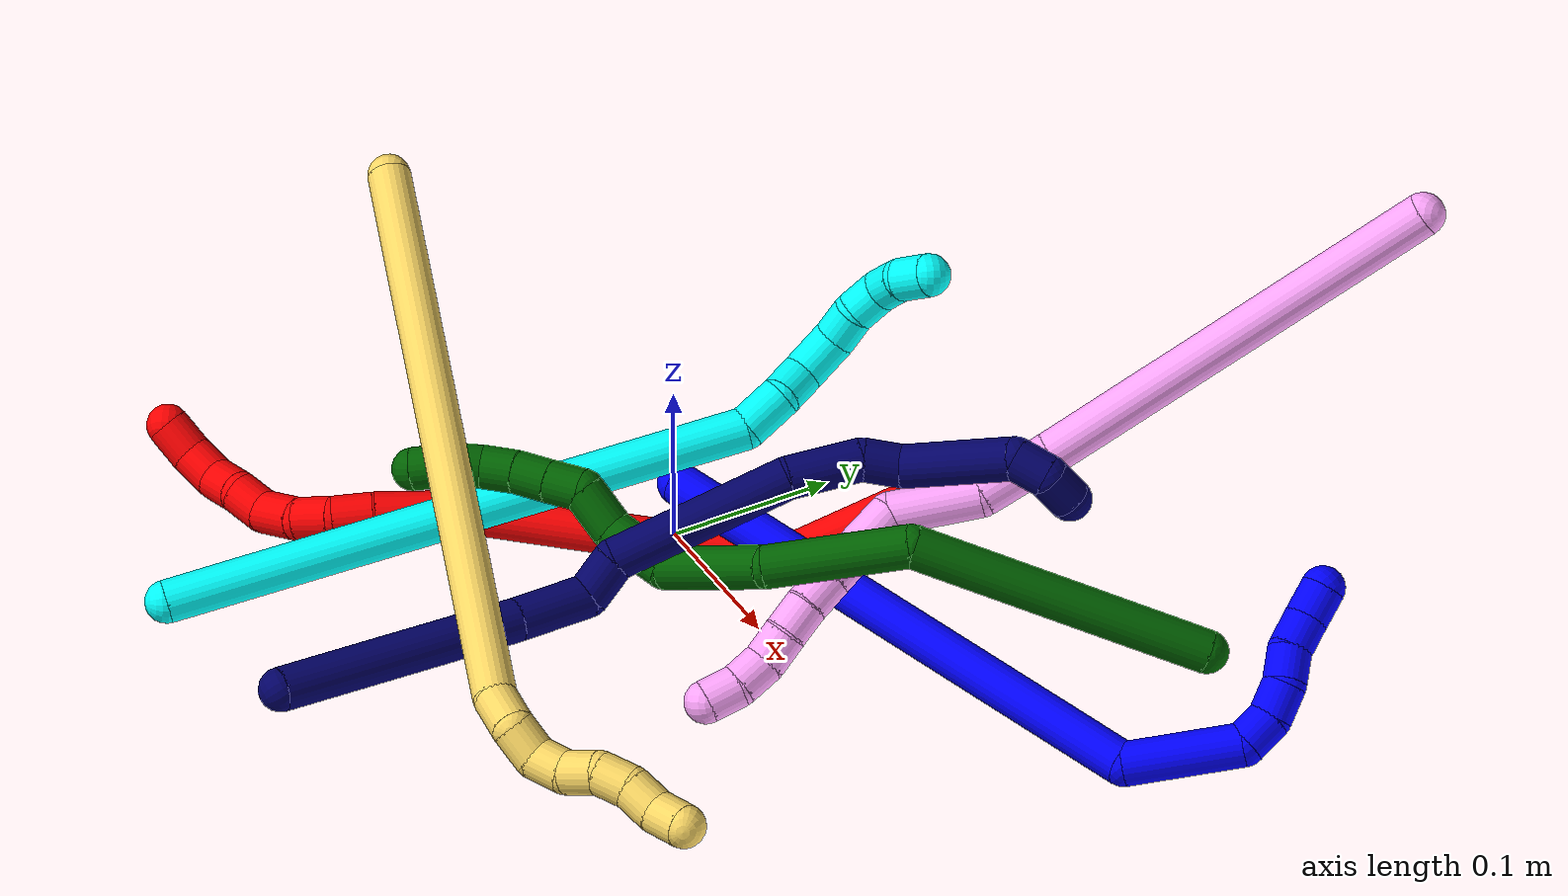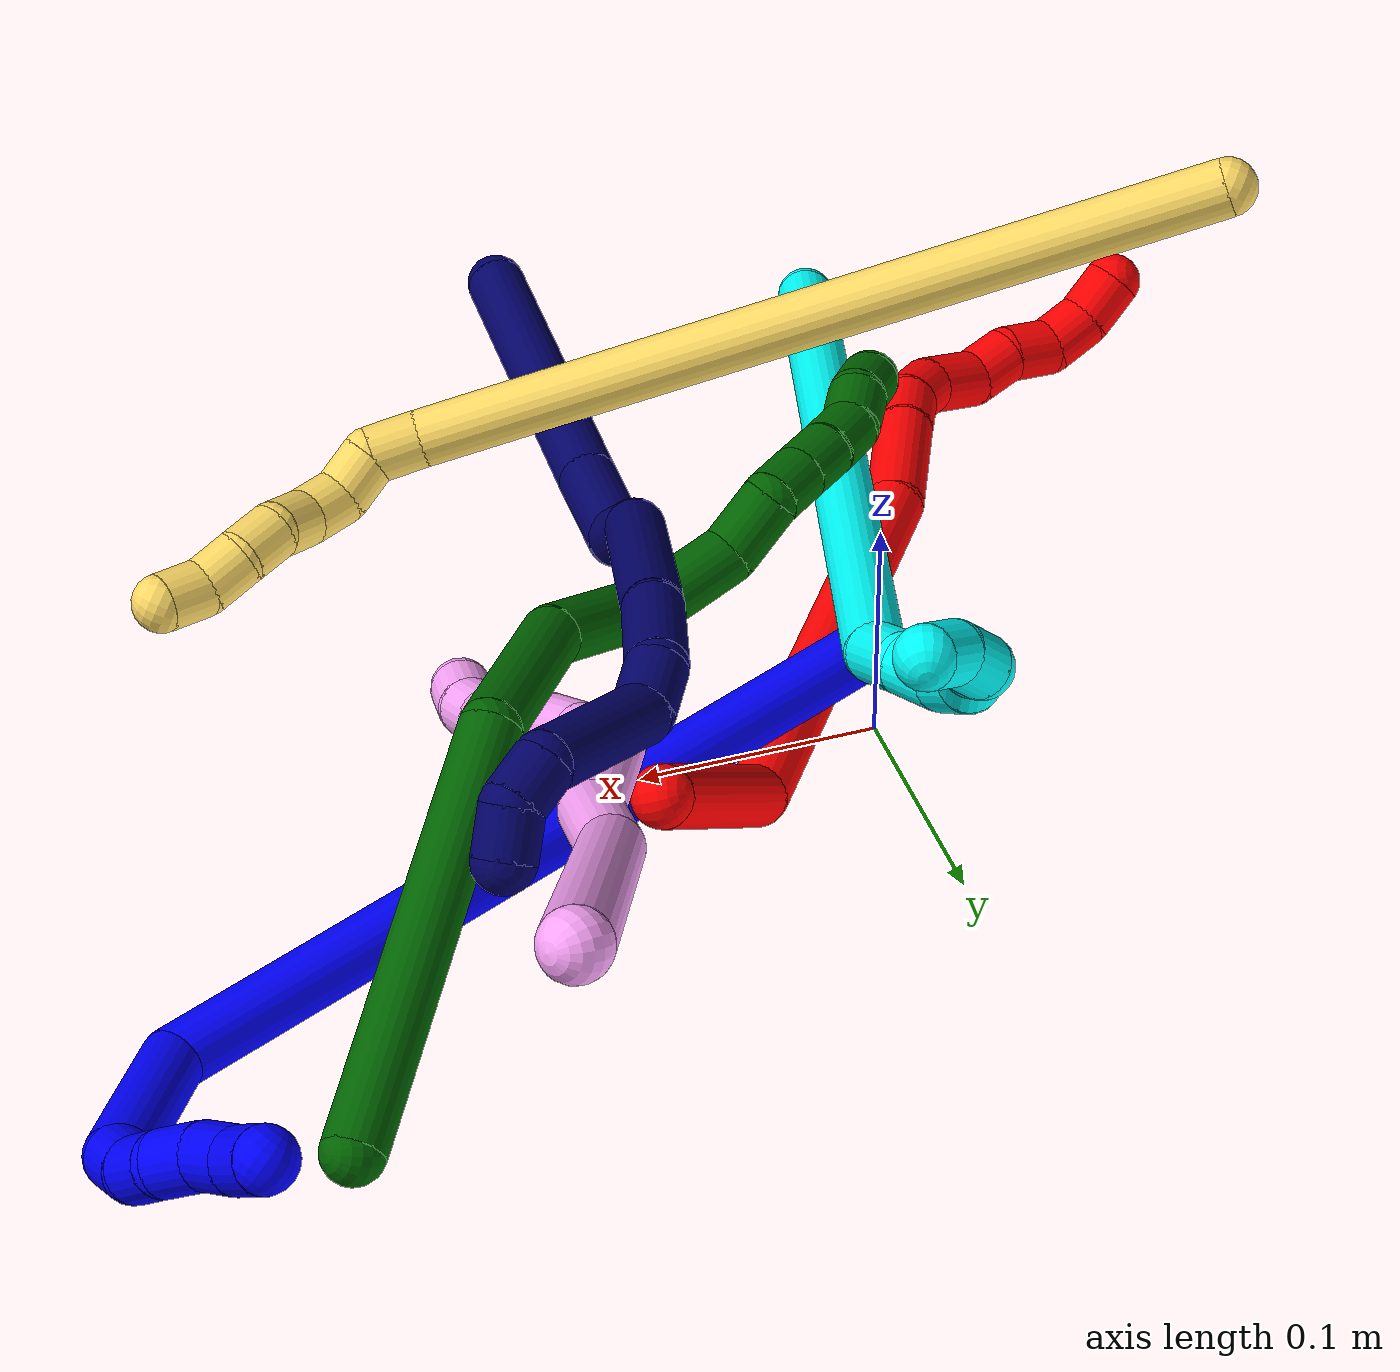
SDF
<sdf version="1.7">
 <world name="default">
  <plugin name="TubeGeneratorPlugin" filename="libtube_generator_plugin.so"/>
  <model name="photoneo_s_sensor">
   <static>1</static>
   <pose>0 0 2 1.57079 1.57079 3.14159</pose>
   <link name="link">
    <inertial><mass>0.1</mass></inertial>
    <sensor name="sensor" type="depth">
     <update_rate>30</update_rate>
     <camera>
      <horizontal_fov>1.22</horizontal_fov>
      <image><width>1920</width><height>1200</height><format>B8G8R8</format></image>
      <clip><near>0.1</near><far>4</far></clip>
      <depth_camera><output>points</output></depth_camera>
     </camera>
     <plugin name="camera_plugin" filename="libgazebo_ros_depth_camera.so">
      <baseline>0.2</baseline>
      <alwaysOn>1</alwaysOn>
      <updateRate>0.0</updateRate>
      <cameraName>camera_ir</cameraName>
      <imageTopicName>/camera/color/image_raw</imageTopicName>
      <cameraInfoTopicName>/camera/color/camera_info</cameraInfoTopicName>
      <depthImageTopicName>/camera/depth/image_raw</depthImageTopicName>
      <depthImageCameraInfoTopicName>/camera/depth/camera_info</depthImageCameraInfoTopicName>
      <pointCloudTopicName>/camera/depth/points</pointCloudTopicName>
      <frameName>fr_optical</frameName>
      <pointCloudCutoff>0.1</pointCloudCutoff>
      <pointCloudCutoffMax>2.0</pointCloudCutoffMax>
      <distortionK1>0</distortionK1>
      <distortionK2>0</distortionK2>
      <distortionK3>0</distortionK3>
      <distortionT1>0</distortionT1>
      <distortionT2>0</distortionT2>
      <CxPrime>0</CxPrime>
      <Cx>0</Cx>
      <Cy>0</Cy>
      <focalLength>0</focalLength>
      <hackBaseline>0</hackBaseline>
     </plugin>
    </sensor>
   </link>
  </model>
  <gravity>0 0 -9.8</gravity>
  <magnetic_field>6e-06 2.3e-05 -4.2e-05</magnetic_field>
  <atmosphere type="adiabatic"/>
  <physics name="default_physics" default="0" type="ode">
   <max_step_size>0.003</max_step_size>
   <real_time_factor>1</real_time_factor>
   <real_time_update_rate>1000</real_time_update_rate>
   <max_contacts>10000</max_contacts>
   <ode>
    <solver>
     <type>quick</type>
     <iters>100</iters>
     <sor>1.3</sor>
     <use_dynamic_moi_rescaling>0</use_dynamic_moi_rescaling>
    </solver>
    <constraints>
     <contact_max_correcting_vel>0</contact_max_correcting_vel>
     <contact_surface_layer>0.001</contact_surface_layer>
     <cfm>0</cfm>
     <erp>0.2</erp>
    </constraints>
   </ode>
  </physics>
  <scene><ambient>0.4 0.4 0.4 1</ambient><background>0.7 0.7 0.7 1</background><shadows>0</shadows></scene>
  <audio><device>default</device></audio>
  <spherical_coordinates>
   <surface_model>EARTH_WGS84</surface_model>
   <latitude_deg>0</latitude_deg>
   <longitude_deg>0</longitude_deg>
   <elevation>0</elevation>
   <heading_deg>0</heading_deg>
  </spherical_coordinates>
  <model name="bin">
   <static>1</static>
   <link name="bottom">
    <collision name="collision-bottom">
     <pose>0 0 -0.01 0 -0 0</pose>
     <geometry><box><size>0.8 0.6 0.02</size></box></geometry>
     <surface>
      <friction><ode><mu>100</mu><mu2>100</mu2></ode></friction>
      <contact><collide_bitmask>65535</collide_bitmask></contact>
     </surface>
    </collision>
   </link>
   <link name="west_wall">
    <collision name="collision-west_wall">
     <pose>-0.41 0 0.1 0 -0 0</pose>
     <geometry><box><size>0.02 0.6 0.2</size></box></geometry>
     <surface>
      <friction><ode><mu>100</mu><mu2>100</mu2></ode></friction>
      <contact><collide_bitmask>65535</collide_bitmask></contact>
     </surface>
    </collision>
   </link>
   <link name="east_wall">
    <collision name="collision-east_wall">
     <pose>0.41 0 0.1 0 -0 0</pose>
     <geometry><box><size>0.02 0.6 0.2</size></box></geometry>
     <surface>
      <friction><ode><mu>100</mu><mu2>100</mu2></ode></friction>
      <contact><collide_bitmask>65535</collide_bitmask></contact>
     </surface>
    </collision>
   </link>
   <link name="south_wall">
    <collision name="collision-south_wall">
     <pose>0 -0.31 0.1 0 -0 0</pose>
     <geometry><box><size>0.8 0.02 0.2</size></box></geometry>
     <surface>
      <friction><ode><mu>100</mu><mu2>100</mu2></ode></friction>
      <contact><collide_bitmask>65535</collide_bitmask></contact>
     </surface>
    </collision>
   </link>
   <link name="north_wall">
    <collision name="collision-north_wall">
     <pose>0 0.31 0.1 0 -0 0</pose>
     <geometry><box><size>0.8 0.02 0.2</size></box></geometry>
     <surface>
      <friction><ode><mu>100</mu><mu2>100</mu2></ode></friction>
      <contact><collide_bitmask>65535</collide_bitmask></contact>
     </surface>
    </collision>
   </link>
  </model>
  <model name="1">
   <static>0</static>
   <link name="1">
    <collision name="collision-cylinder-e_1_1_4">
     <pose>0.090109 0.019213 0.137033 -0.139298 0.577221 -0.041419</pose>
     <geometry><cylinder><radius>0.0125</radius><length>0.330253</length></cylinder></geometry>
     <surface>
      <friction><ode><mu>1.16</mu><mu2>1.16</mu2><slip1>0</slip1><slip2>0</slip2></ode></friction>
      <contact><ode><kp>1e+06</kp><kd>1</kd><max_vel>0</max_vel><min_depth>0.001</min_depth></ode></contact>
     </surface>
    </collision>
    <visual name="visual-cylinder-e_1_1_4">
     <pose>0.090109 0.019213 0.137033 -0.139298 0.577221 -0.041419</pose>
     <geometry><cylinder><radius>0.0125</radius><length>0.330253</length></cylinder></geometry>
     <material><ambient>0 0 1 1</ambient></material>
    </visual>
    <collision name="collision-cylinder-e_2_4_5">
     <pose>0.20441 0.020846 0.29007 0.832246 0.794103 0.366465</pose>
     <geometry><cylinder><radius>0.0125</radius><length>0.067836</length></cylinder></geometry>
     <surface>
      <friction><ode><mu>1.16</mu><mu2>1.16</mu2><slip1>0</slip1><slip2>0</slip2></ode></friction>
      <contact><ode><kp>1e+06</kp><kd>1</kd><max_vel>0</max_vel><min_depth>0.001</min_depth></ode></contact>
     </surface>
    </collision>
    <visual name="visual-cylinder-e_2_4_5">
     <pose>0.20441 0.020846 0.29007 0.832246 0.794103 0.366465</pose>
     <geometry><cylinder><radius>0.0125</radius><length>0.067836</length></cylinder></geometry>
     <material><ambient>0 0 1 1</ambient></material>
    </visual>
    <collision name="collision-cylinder-e_3_5_6">
     <pose>0.234418 -0.005174 0.304811 1.7195 0.598228 0.687575</pose>
     <geometry><cylinder><radius>0.0125</radius><length>0.020657</length></cylinder></geometry>
     <surface>
      <friction><ode><mu>1.16</mu><mu2>1.16</mu2><slip1>0</slip1><slip2>0</slip2></ode></friction>
      <contact><ode><kp>1e+06</kp><kd>1</kd><max_vel>0</max_vel><min_depth>0.001</min_depth></ode></contact>
     </surface>
    </collision>
    <visual name="visual-cylinder-e_3_5_6">
     <pose>0.234418 -0.005174 0.304811 1.7195 0.598228 0.687575</pose>
     <geometry><cylinder><radius>0.0125</radius><length>0.020657</length></cylinder></geometry>
     <material><ambient>0 0 1 1</ambient></material>
    </visual>
    <collision name="collision-cylinder-e_4_6_7">
     <pose>0.245725 -0.02079 0.298716 2.16326 0.56563 0.999417</pose>
     <geometry><cylinder><radius>0.0125</radius><length>0.02049</length></cylinder></geometry>
     <surface>
      <friction><ode><mu>1.16</mu><mu2>1.16</mu2><slip1>0</slip1><slip2>0</slip2></ode></friction>
      <contact><ode><kp>1e+06</kp><kd>1</kd><max_vel>0</max_vel><min_depth>0.001</min_depth></ode></contact>
     </surface>
    </collision>
    <visual name="visual-cylinder-e_4_6_7">
     <pose>0.245725 -0.02079 0.298716 2.16326 0.56563 0.999417</pose>
     <geometry><cylinder><radius>0.0125</radius><length>0.02049</length></cylinder></geometry>
     <material><ambient>0 0 1 1</ambient></material>
    </visual>
    <collision name="collision-cylinder-e_5_7_8">
     <pose>0.253654 -0.035537 0.287605 2.26327 0.242904 0.508404</pose>
     <geometry><cylinder><radius>0.0125</radius><length>0.020272</length></cylinder></geometry>
     <surface>
      <friction><ode><mu>1.16</mu><mu2>1.16</mu2><slip1>0</slip1><slip2>0</slip2></ode></friction>
      <contact><ode><kp>1e+06</kp><kd>1</kd><max_vel>0</max_vel><min_depth>0.001</min_depth></ode></contact>
     </surface>
    </collision>
    <visual name="visual-cylinder-e_5_7_8">
     <pose>0.253654 -0.035537 0.287605 2.26327 0.242904 0.508404</pose>
     <geometry><cylinder><radius>0.0125</radius><length>0.020272</length></cylinder></geometry>
     <material><ambient>0 0 1 1</ambient></material>
    </visual>
    <collision name="collision-cylinder-e_6_8_9">
     <pose>0.260055 -0.05172 0.277571 1.98182 0.39932 0.599274</pose>
     <geometry><cylinder><radius>0.0125</radius><length>0.020388</length></cylinder></geometry>
     <surface>
      <friction><ode><mu>1.16</mu><mu2>1.16</mu2><slip1>0</slip1><slip2>0</slip2></ode></friction>
      <contact><ode><kp>1e+06</kp><kd>1</kd><max_vel>0</max_vel><min_depth>0.001</min_depth></ode></contact>
     </surface>
    </collision>
    <visual name="visual-cylinder-e_6_8_9">
     <pose>0.260055 -0.05172 0.277571 1.98182 0.39932 0.599274</pose>
     <geometry><cylinder><radius>0.0125</radius><length>0.020388</length></cylinder></geometry>
     <material><ambient>0 0 1 1</ambient></material>
    </visual>
    <collision name="collision-cylinder-e_7_9_2">
     <pose>0.269637 -0.067724 0.269972 2.0505 0.593061 0.932674</pose>
     <geometry><cylinder><radius>0.0125</radius><length>0.020104</length></cylinder></geometry>
     <surface>
      <friction><ode><mu>1.16</mu><mu2>1.16</mu2><slip1>0</slip1><slip2>0</slip2></ode></friction>
      <contact><ode><kp>1e+06</kp><kd>1</kd><max_vel>0</max_vel><min_depth>0.001</min_depth></ode></contact>
     </surface>
    </collision>
    <visual name="visual-cylinder-e_7_9_2">
     <pose>0.269637 -0.067724 0.269972 2.0505 0.593061 0.932674</pose>
     <geometry><cylinder><radius>0.0125</radius><length>0.020104</length></cylinder></geometry>
     <material><ambient>0 0 1 1</ambient></material>
    </visual>
    <collision name="collision-sphere-2">
     <pose>0.275255 -0.075119 0.266125 0 -0 0</pose>
     <geometry><sphere><radius>0.0125</radius></sphere></geometry>
     <surface>
      <friction><ode><mu>1.16</mu><mu2>1.16</mu2><slip1>0</slip1><slip2>0</slip2></ode></friction>
      <contact><ode><kp>1e+06</kp><kd>1</kd><max_vel>0</max_vel><min_depth>0.001</min_depth></ode></contact>
     </surface>
    </collision>
    <visual name="visual-sphere-2">
     <pose>0.275255 -0.075119 0.266125 0 -0 0</pose>
     <geometry><sphere><radius>0.0125</radius></sphere></geometry>
     <material><ambient>0 0 1 1</ambient></material>
    </visual>
    <collision name="collision-sphere-9">
     <pose>0.264019 -0.060329 0.273819 0 -0 0</pose>
     <geometry><sphere><radius>0.0125</radius></sphere></geometry>
     <surface>
      <friction><ode><mu>1.16</mu><mu2>1.16</mu2><slip1>0</slip1><slip2>0</slip2></ode></friction>
      <contact><ode><kp>1e+06</kp><kd>1</kd><max_vel>0</max_vel><min_depth>0.001</min_depth></ode></contact>
     </surface>
    </collision>
    <visual name="visual-sphere-9">
     <pose>0.264019 -0.060329 0.273819 0 -0 0</pose>
     <geometry><sphere><radius>0.0125</radius></sphere></geometry>
     <material><ambient>0 0 1 1</ambient></material>
    </visual>
    <collision name="collision-sphere-4">
     <pose>0.180218 0.038426 0.274066 0 -0 0</pose>
     <geometry><sphere><radius>0.0125</radius></sphere></geometry>
     <surface>
      <friction><ode><mu>1.16</mu><mu2>1.16</mu2><slip1>0</slip1><slip2>0</slip2></ode></friction>
      <contact><ode><kp>1e+06</kp><kd>1</kd><max_vel>0</max_vel><min_depth>0.001</min_depth></ode></contact>
     </surface>
    </collision>
    <visual name="visual-sphere-4">
     <pose>0.180218 0.038426 0.274066 0 -0 0</pose>
     <geometry><sphere><radius>0.0125</radius></sphere></geometry>
     <material><ambient>0 0 1 1</ambient></material>
    </visual>
    <collision name="collision-sphere-1">
     <geometry><sphere><radius>0.0125</radius></sphere></geometry>
     <surface>
      <friction><ode><mu>1.16</mu><mu2>1.16</mu2><slip1>0</slip1><slip2>0</slip2></ode></friction>
      <contact><ode><kp>1e+06</kp><kd>1</kd><max_vel>0</max_vel><min_depth>0.001</min_depth></ode></contact>
     </surface>
    </collision>
    <visual name="visual-sphere-1">
     <geometry><sphere><radius>0.0125</radius></sphere></geometry>
     <material><ambient>0 0 1 1</ambient></material>
    </visual>
    <collision name="collision-sphere-8">
     <pose>0.256092 -0.04311 0.281324 0 -0 0</pose>
     <geometry><sphere><radius>0.0125</radius></sphere></geometry>
     <surface>
      <friction><ode><mu>1.16</mu><mu2>1.16</mu2><slip1>0</slip1><slip2>0</slip2></ode></friction>
      <contact><ode><kp>1e+06</kp><kd>1</kd><max_vel>0</max_vel><min_depth>0.001</min_depth></ode></contact>
     </surface>
    </collision>
    <visual name="visual-sphere-8">
     <pose>0.256092 -0.04311 0.281324 0 -0 0</pose>
     <geometry><sphere><radius>0.0125</radius></sphere></geometry>
     <material><ambient>0 0 1 1</ambient></material>
    </visual>
    <collision name="collision-sphere-5">
     <pose>0.228601 0.003267 0.306075 0 -0 0</pose>
     <geometry><sphere><radius>0.0125</radius></sphere></geometry>
     <surface>
      <friction><ode><mu>1.16</mu><mu2>1.16</mu2><slip1>0</slip1><slip2>0</slip2></ode></friction>
      <contact><ode><kp>1e+06</kp><kd>1</kd><max_vel>0</max_vel><min_depth>0.001</min_depth></ode></contact>
     </surface>
    </collision>
    <visual name="visual-sphere-5">
     <pose>0.228601 0.003267 0.306075 0 -0 0</pose>
     <geometry><sphere><radius>0.0125</radius></sphere></geometry>
     <material><ambient>0 0 1 1</ambient></material>
    </visual>
    <collision name="collision-sphere-6">
     <pose>0.240235 -0.013615 0.303546 0 -0 0</pose>
     <geometry><sphere><radius>0.0125</radius></sphere></geometry>
     <surface>
      <friction><ode><mu>1.16</mu><mu2>1.16</mu2><slip1>0</slip1><slip2>0</slip2></ode></friction>
      <contact><ode><kp>1e+06</kp><kd>1</kd><max_vel>0</max_vel><min_depth>0.001</min_depth></ode></contact>
     </surface>
    </collision>
    <visual name="visual-sphere-6">
     <pose>0.240235 -0.013615 0.303546 0 -0 0</pose>
     <geometry><sphere><radius>0.0125</radius></sphere></geometry>
     <material><ambient>0 0 1 1</ambient></material>
    </visual>
    <collision name="collision-sphere-7">
     <pose>0.251216 -0.027965 0.293887 0 -0 0</pose>
     <geometry><sphere><radius>0.0125</radius></sphere></geometry>
     <surface>
      <friction><ode><mu>1.16</mu><mu2>1.16</mu2><slip1>0</slip1><slip2>0</slip2></ode></friction>
      <contact><ode><kp>1e+06</kp><kd>1</kd><max_vel>0</max_vel><min_depth>0.001</min_depth></ode></contact>
     </surface>
    </collision>
    <visual name="visual-sphere-7">
     <pose>0.251216 -0.027965 0.293887 0 -0 0</pose>
     <geometry><sphere><radius>0.0125</radius></sphere></geometry>
     <material><ambient>0 0 1 1</ambient></material>
    </visual>
    <inertial>
     <pose>0.138735 0.00818 0.188534 0 -0 0</pose>
     <mass>0.5</mass>
     <inertia>
      <ixx>0.002476</ixx>
      <ixy>0</ixy>
      <ixz>0</ixz>
      <iyy>0.002917</iyy>
      <iyz>0</iyz>
      <izz>-0.001978</izz>
     </inertia>
    </inertial>
   </link>
   <pose>0.006616 -0.000606 0.041403 3.02345 -0.885798 0.560304</pose>
  </model>
  <model name="2">
   <static>0</static>
   <link name="2">
    <collision name="collision-cylinder-e_1_1_4">
     <pose>-0.006776 -0.050762 0.006327 1.44679 -0.13169 -0.116331</pose>
     <geometry><cylinder><radius>0.0125</radius><length>0.103202</length></cylinder></geometry>
     <surface>
      <friction><ode><mu>1.16</mu><mu2>1.16</mu2><slip1>0</slip1><slip2>0</slip2></ode></friction>
      <contact><ode><kp>1e+06</kp><kd>1</kd><max_vel>0</max_vel><min_depth>0.001</min_depth></ode></contact>
     </surface>
    </collision>
    <visual name="visual-cylinder-e_1_1_4">
     <pose>-0.006776 -0.050762 0.006327 1.44679 -0.13169 -0.116331</pose>
     <geometry><cylinder><radius>0.0125</radius><length>0.103202</length></cylinder></geometry>
     <material><ambient>1 0 0 1</ambient></material>
    </visual>
    <collision name="collision-cylinder-e_2_4_5">
     <pose>-0.082125 -0.163801 0.004643 1.69874 -0.829389 -0.928073</pose>
     <geometry><cylinder><radius>0.0125</radius><length>0.185957</length></cylinder></geometry>
     <surface>
      <friction><ode><mu>1.16</mu><mu2>1.16</mu2><slip1>0</slip1><slip2>0</slip2></ode></friction>
      <contact><ode><kp>1e+06</kp><kd>1</kd><max_vel>0</max_vel><min_depth>0.001</min_depth></ode></contact>
     </surface>
    </collision>
    <visual name="visual-cylinder-e_2_4_5">
     <pose>-0.082125 -0.163801 0.004643 1.69874 -0.829389 -0.928073</pose>
     <geometry><cylinder><radius>0.0125</radius><length>0.185957</length></cylinder></geometry>
     <material><ambient>1 0 0 1</ambient></material>
    </visual>
    <collision name="collision-cylinder-e_3_5_6">
     <pose>-0.170651 -0.242065 -0.000107 1.36953 -0.885347 -0.738665</pose>
     <geometry><cylinder><radius>0.0125</radius><length>0.051549</length></cylinder></geometry>
     <surface>
      <friction><ode><mu>1.16</mu><mu2>1.16</mu2><slip1>0</slip1><slip2>0</slip2></ode></friction>
      <contact><ode><kp>1e+06</kp><kd>1</kd><max_vel>0</max_vel><min_depth>0.001</min_depth></ode></contact>
     </surface>
    </collision>
    <visual name="visual-cylinder-e_3_5_6">
     <pose>-0.170651 -0.242065 -0.000107 1.36953 -0.885347 -0.738665</pose>
     <geometry><cylinder><radius>0.0125</radius><length>0.051549</length></cylinder></geometry>
     <material><ambient>1 0 0 1</ambient></material>
    </visual>
    <collision name="collision-cylinder-e_4_6_7">
     <pose>-0.198916 -0.266351 0.005111 1.33925 -0.772568 -0.622986</pose>
     <geometry><cylinder><radius>0.0125</radius><length>0.023816</length></cylinder></geometry>
     <surface>
      <friction><ode><mu>1.16</mu><mu2>1.16</mu2><slip1>0</slip1><slip2>0</slip2></ode></friction>
      <contact><ode><kp>1e+06</kp><kd>1</kd><max_vel>0</max_vel><min_depth>0.001</min_depth></ode></contact>
     </surface>
    </collision>
    <visual name="visual-cylinder-e_4_6_7">
     <pose>-0.198916 -0.266351 0.005111 1.33925 -0.772568 -0.622986</pose>
     <geometry><cylinder><radius>0.0125</radius><length>0.023816</length></cylinder></geometry>
     <material><ambient>1 0 0 1</ambient></material>
    </visual>
    <collision name="collision-cylinder-e_5_7_8">
     <pose>-0.212407 -0.284014 0.006461 1.63559 -0.504425 -0.536664</pose>
     <geometry><cylinder><radius>0.0125</radius><length>0.021435</length></cylinder></geometry>
     <surface>
      <friction><ode><mu>1.16</mu><mu2>1.16</mu2><slip1>0</slip1><slip2>0</slip2></ode></friction>
      <contact><ode><kp>1e+06</kp><kd>1</kd><max_vel>0</max_vel><min_depth>0.001</min_depth></ode></contact>
     </surface>
    </collision>
    <visual name="visual-cylinder-e_5_7_8">
     <pose>-0.212407 -0.284014 0.006461 1.63559 -0.504425 -0.536664</pose>
     <geometry><cylinder><radius>0.0125</radius><length>0.021435</length></cylinder></geometry>
     <material><ambient>1 0 0 1</ambient></material>
    </visual>
    <collision name="collision-cylinder-e_6_8_9">
     <pose>-0.220499 -0.306044 0.000545 1.96766 -0.208913 -0.312651</pose>
     <geometry><cylinder><radius>0.0125</radius><length>0.028078</length></cylinder></geometry>
     <surface>
      <friction><ode><mu>1.16</mu><mu2>1.16</mu2><slip1>0</slip1><slip2>0</slip2></ode></friction>
      <contact><ode><kp>1e+06</kp><kd>1</kd><max_vel>0</max_vel><min_depth>0.001</min_depth></ode></contact>
     </surface>
    </collision>
    <visual name="visual-cylinder-e_6_8_9">
     <pose>-0.220499 -0.306044 0.000545 1.96766 -0.208913 -0.312651</pose>
     <geometry><cylinder><radius>0.0125</radius><length>0.028078</length></cylinder></geometry>
     <material><ambient>1 0 0 1</ambient></material>
    </visual>
    <collision name="collision-cylinder-e_7_9_10">
     <pose>-0.228805 -0.324906 -0.01106 2.36417 -0.54821 -1.20331</pose>
     <geometry><cylinder><radius>0.0125</radius><length>0.020702</length></cylinder></geometry>
     <surface>
      <friction><ode><mu>1.16</mu><mu2>1.16</mu2><slip1>0</slip1><slip2>0</slip2></ode></friction>
      <contact><ode><kp>1e+06</kp><kd>1</kd><max_vel>0</max_vel><min_depth>0.001</min_depth></ode></contact>
     </surface>
    </collision>
    <visual name="visual-cylinder-e_7_9_10">
     <pose>-0.228805 -0.324906 -0.01106 2.36417 -0.54821 -1.20331</pose>
     <geometry><cylinder><radius>0.0125</radius><length>0.020702</length></cylinder></geometry>
     <material><ambient>1 0 0 1</ambient></material>
    </visual>
    <collision name="collision-cylinder-e_8_10_11">
     <pose>-0.236248 -0.339937 -0.023804 2.20128 -0.185183 -0.361473</pose>
     <geometry><cylinder><radius>0.0125</radius><length>0.022255</length></cylinder></geometry>
     <surface>
      <friction><ode><mu>1.16</mu><mu2>1.16</mu2><slip1>0</slip1><slip2>0</slip2></ode></friction>
      <contact><ode><kp>1e+06</kp><kd>1</kd><max_vel>0</max_vel><min_depth>0.001</min_depth></ode></contact>
     </surface>
    </collision>
    <visual name="visual-cylinder-e_8_10_11">
     <pose>-0.236248 -0.339937 -0.023804 2.20128 -0.185183 -0.361473</pose>
     <geometry><cylinder><radius>0.0125</radius><length>0.022255</length></cylinder></geometry>
     <material><ambient>1 0 0 1</ambient></material>
    </visual>
    <collision name="collision-cylinder-e_9_11_12">
     <pose>-0.244164 -0.353996 -0.037488 2.51622 -0.581523 -1.49357</pose>
     <geometry><cylinder><radius>0.0125</radius><length>0.021362</length></cylinder></geometry>
     <surface>
      <friction><ode><mu>1.16</mu><mu2>1.16</mu2><slip1>0</slip1><slip2>0</slip2></ode></friction>
      <contact><ode><kp>1e+06</kp><kd>1</kd><max_vel>0</max_vel><min_depth>0.001</min_depth></ode></contact>
     </surface>
    </collision>
    <visual name="visual-cylinder-e_9_11_12">
     <pose>-0.244164 -0.353996 -0.037488 2.51622 -0.581523 -1.49357</pose>
     <geometry><cylinder><radius>0.0125</radius><length>0.021362</length></cylinder></geometry>
     <material><ambient>1 0 0 1</ambient></material>
    </visual>
    <collision name="collision-cylinder-e_10_12_2">
     <pose>-0.257864 -0.361658 -0.051782 2.80914 -0.809352 -2.39493</pose>
     <geometry><cylinder><radius>0.0125</radius><length>0.021645</length></cylinder></geometry>
     <surface>
      <friction><ode><mu>1.16</mu><mu2>1.16</mu2><slip1>0</slip1><slip2>0</slip2></ode></friction>
      <contact><ode><kp>1e+06</kp><kd>1</kd><max_vel>0</max_vel><min_depth>0.001</min_depth></ode></contact>
     </surface>
    </collision>
    <visual name="visual-cylinder-e_10_12_2">
     <pose>-0.257864 -0.361658 -0.051782 2.80914 -0.809352 -2.39493</pose>
     <geometry><cylinder><radius>0.0125</radius><length>0.021645</length></cylinder></geometry>
     <material><ambient>1 0 0 1</ambient></material>
    </visual>
    <collision name="collision-sphere-2">
     <pose>-0.265698 -0.364095 -0.05884 0 -0 0</pose>
     <geometry><sphere><radius>0.0125</radius></sphere></geometry>
     <surface>
      <friction><ode><mu>1.16</mu><mu2>1.16</mu2><slip1>0</slip1><slip2>0</slip2></ode></friction>
      <contact><ode><kp>1e+06</kp><kd>1</kd><max_vel>0</max_vel><min_depth>0.001</min_depth></ode></contact>
     </surface>
    </collision>
    <visual name="visual-sphere-2">
     <pose>-0.265698 -0.364095 -0.05884 0 -0 0</pose>
     <geometry><sphere><radius>0.0125</radius></sphere></geometry>
     <material><ambient>1 0 0 1</ambient></material>
    </visual>
    <collision name="collision-sphere-12">
     <pose>-0.250031 -0.359221 -0.044724 0 -0 0</pose>
     <geometry><sphere><radius>0.0125</radius></sphere></geometry>
     <surface>
      <friction><ode><mu>1.16</mu><mu2>1.16</mu2><slip1>0</slip1><slip2>0</slip2></ode></friction>
      <contact><ode><kp>1e+06</kp><kd>1</kd><max_vel>0</max_vel><min_depth>0.001</min_depth></ode></contact>
     </surface>
    </collision>
    <visual name="visual-sphere-12">
     <pose>-0.250031 -0.359221 -0.044724 0 -0 0</pose>
     <geometry><sphere><radius>0.0125</radius></sphere></geometry>
     <material><ambient>1 0 0 1</ambient></material>
    </visual>
    <collision name="collision-sphere-11">
     <pose>-0.238297 -0.348772 -0.030252 0 -0 0</pose>
     <geometry><sphere><radius>0.0125</radius></sphere></geometry>
     <surface>
      <friction><ode><mu>1.16</mu><mu2>1.16</mu2><slip1>0</slip1><slip2>0</slip2></ode></friction>
      <contact><ode><kp>1e+06</kp><kd>1</kd><max_vel>0</max_vel><min_depth>0.001</min_depth></ode></contact>
     </surface>
    </collision>
    <visual name="visual-sphere-11">
     <pose>-0.238297 -0.348772 -0.030252 0 -0 0</pose>
     <geometry><sphere><radius>0.0125</radius></sphere></geometry>
     <material><ambient>1 0 0 1</ambient></material>
    </visual>
    <collision name="collision-sphere-10">
     <pose>-0.234199 -0.331103 -0.017356 0 -0 0</pose>
     <geometry><sphere><radius>0.0125</radius></sphere></geometry>
     <surface>
      <friction><ode><mu>1.16</mu><mu2>1.16</mu2><slip1>0</slip1><slip2>0</slip2></ode></friction>
      <contact><ode><kp>1e+06</kp><kd>1</kd><max_vel>0</max_vel><min_depth>0.001</min_depth></ode></contact>
     </surface>
    </collision>
    <visual name="visual-sphere-10">
     <pose>-0.234199 -0.331103 -0.017356 0 -0 0</pose>
     <geometry><sphere><radius>0.0125</radius></sphere></geometry>
     <material><ambient>1 0 0 1</ambient></material>
    </visual>
    <collision name="collision-sphere-9">
     <pose>-0.22341 -0.31871 -0.004764 0 -0 0</pose>
     <geometry><sphere><radius>0.0125</radius></sphere></geometry>
     <surface>
      <friction><ode><mu>1.16</mu><mu2>1.16</mu2><slip1>0</slip1><slip2>0</slip2></ode></friction>
      <contact><ode><kp>1e+06</kp><kd>1</kd><max_vel>0</max_vel><min_depth>0.001</min_depth></ode></contact>
     </surface>
    </collision>
    <visual name="visual-sphere-9">
     <pose>-0.22341 -0.31871 -0.004764 0 -0 0</pose>
     <geometry><sphere><radius>0.0125</radius></sphere></geometry>
     <material><ambient>1 0 0 1</ambient></material>
    </visual>
    <collision name="collision-sphere-4">
     <pose>-0.013551 -0.101523 0.012655 0 -0 0</pose>
     <geometry><sphere><radius>0.0125</radius></sphere></geometry>
     <surface>
      <friction><ode><mu>1.16</mu><mu2>1.16</mu2><slip1>0</slip1><slip2>0</slip2></ode></friction>
      <contact><ode><kp>1e+06</kp><kd>1</kd><max_vel>0</max_vel><min_depth>0.001</min_depth></ode></contact>
     </surface>
    </collision>
    <visual name="visual-sphere-4">
     <pose>-0.013551 -0.101523 0.012655 0 -0 0</pose>
     <geometry><sphere><radius>0.0125</radius></sphere></geometry>
     <material><ambient>1 0 0 1</ambient></material>
    </visual>
    <collision name="collision-sphere-1">
     <geometry><sphere><radius>0.0125</radius></sphere></geometry>
     <surface>
      <friction><ode><mu>1.16</mu><mu2>1.16</mu2><slip1>0</slip1><slip2>0</slip2></ode></friction>
      <contact><ode><kp>1e+06</kp><kd>1</kd><max_vel>0</max_vel><min_depth>0.001</min_depth></ode></contact>
     </surface>
    </collision>
    <visual name="visual-sphere-1">
     <geometry><sphere><radius>0.0125</radius></sphere></geometry>
     <material><ambient>1 0 0 1</ambient></material>
    </visual>
    <collision name="collision-sphere-8">
     <pose>-0.217587 -0.293378 0.005853 0 -0 0</pose>
     <geometry><sphere><radius>0.0125</radius></sphere></geometry>
     <surface>
      <friction><ode><mu>1.16</mu><mu2>1.16</mu2><slip1>0</slip1><slip2>0</slip2></ode></friction>
      <contact><ode><kp>1e+06</kp><kd>1</kd><max_vel>0</max_vel><min_depth>0.001</min_depth></ode></contact>
     </surface>
    </collision>
    <visual name="visual-sphere-8">
     <pose>-0.217587 -0.293378 0.005853 0 -0 0</pose>
     <geometry><sphere><radius>0.0125</radius></sphere></geometry>
     <material><ambient>1 0 0 1</ambient></material>
    </visual>
    <collision name="collision-sphere-5">
     <pose>-0.150698 -0.226078 -0.003369 0 -0 0</pose>
     <geometry><sphere><radius>0.0125</radius></sphere></geometry>
     <surface>
      <friction><ode><mu>1.16</mu><mu2>1.16</mu2><slip1>0</slip1><slip2>0</slip2></ode></friction>
      <contact><ode><kp>1e+06</kp><kd>1</kd><max_vel>0</max_vel><min_depth>0.001</min_depth></ode></contact>
     </surface>
    </collision>
    <visual name="visual-sphere-5">
     <pose>-0.150698 -0.226078 -0.003369 0 -0 0</pose>
     <geometry><sphere><radius>0.0125</radius></sphere></geometry>
     <material><ambient>1 0 0 1</ambient></material>
    </visual>
    <collision name="collision-sphere-6">
     <pose>-0.190604 -0.258051 0.003154 0 -0 0</pose>
     <geometry><sphere><radius>0.0125</radius></sphere></geometry>
     <surface>
      <friction><ode><mu>1.16</mu><mu2>1.16</mu2><slip1>0</slip1><slip2>0</slip2></ode></friction>
      <contact><ode><kp>1e+06</kp><kd>1</kd><max_vel>0</max_vel><min_depth>0.001</min_depth></ode></contact>
     </surface>
    </collision>
    <visual name="visual-sphere-6">
     <pose>-0.190604 -0.258051 0.003154 0 -0 0</pose>
     <geometry><sphere><radius>0.0125</radius></sphere></geometry>
     <material><ambient>1 0 0 1</ambient></material>
    </visual>
    <collision name="collision-sphere-7">
     <pose>-0.207227 -0.274651 0.007068 0 -0 0</pose>
     <geometry><sphere><radius>0.0125</radius></sphere></geometry>
     <surface>
      <friction><ode><mu>1.16</mu><mu2>1.16</mu2><slip1>0</slip1><slip2>0</slip2></ode></friction>
      <contact><ode><kp>1e+06</kp><kd>1</kd><max_vel>0</max_vel><min_depth>0.001</min_depth></ode></contact>
     </surface>
    </collision>
    <visual name="visual-sphere-7">
     <pose>-0.207227 -0.274651 0.007068 0 -0 0</pose>
     <geometry><sphere><radius>0.0125</radius></sphere></geometry>
     <material><ambient>1 0 0 1</ambient></material>
    </visual>
    <inertial>
     <pose>-0.122081 -0.197765 -0.001788 0 -0 0</pose>
     <mass>0.5</mass>
     <inertia><ixx>-1.1e-05</ixx><ixy>0</ixy><ixz>0</ixz><iyy>-4.5e-05</iyy><iyz>0</iyz><izz>0.0009</izz></inertia>
    </inertial>
   </link>
   <pose>0.121318 0.09525 0.073827 2.16063 0.683182 1.38052</pose>
  </model>
  <model name="3">
   <static>0</static>
   <link name="3">
    <collision name="collision-cylinder-e_1_1_4">
     <pose>0.001794 0.045389 -0.165852 -2.87446 0.010436 -0.077627</pose>
     <geometry><cylinder><radius>0.0125</radius><length>0.34392</length></cylinder></geometry>
     <surface>
      <friction><ode><mu>1.16</mu><mu2>1.16</mu2><slip1>0</slip1><slip2>0</slip2></ode></friction>
      <contact><ode><kp>1e+06</kp><kd>1</kd><max_vel>0</max_vel><min_depth>0.001</min_depth></ode></contact>
     </surface>
    </collision>
    <visual name="visual-cylinder-e_1_1_4">
     <pose>0.001794 0.045389 -0.165852 -2.87446 0.010436 -0.077627</pose>
     <geometry><cylinder><radius>0.0125</radius><length>0.34392</length></cylinder></geometry>
     <material><ambient>0.003922 1 0.996078 1</ambient></material>
    </visual>
    <collision name="collision-cylinder-e_2_4_5">
     <pose>0.000135 0.098575 -0.342297 -2.50716 -0.256774 0.74931</pose>
     <geometry><cylinder><radius>0.0125</radius><length>0.027199</length></cylinder></geometry>
     <surface>
      <friction><ode><mu>1.16</mu><mu2>1.16</mu2><slip1>0</slip1><slip2>0</slip2></ode></friction>
      <contact><ode><kp>1e+06</kp><kd>1</kd><max_vel>0</max_vel><min_depth>0.001</min_depth></ode></contact>
     </surface>
    </collision>
    <visual name="visual-cylinder-e_2_4_5">
     <pose>0.000135 0.098575 -0.342297 -2.50716 -0.256774 0.74931</pose>
     <geometry><cylinder><radius>0.0125</radius><length>0.027199</length></cylinder></geometry>
     <material><ambient>0.003922 1 0.996078 1</ambient></material>
    </visual>
    <collision name="collision-cylinder-e_3_5_6">
     <pose>-0.009731 0.110039 -0.360492 -2.69192 -0.649716 1.94851</pose>
     <geometry><cylinder><radius>0.0125</radius><length>0.021198</length></cylinder></geometry>
     <surface>
      <friction><ode><mu>1.16</mu><mu2>1.16</mu2><slip1>0</slip1><slip2>0</slip2></ode></friction>
      <contact><ode><kp>1e+06</kp><kd>1</kd><max_vel>0</max_vel><min_depth>0.001</min_depth></ode></contact>
     </surface>
    </collision>
    <visual name="visual-cylinder-e_3_5_6">
     <pose>-0.009731 0.110039 -0.360492 -2.69192 -0.649716 1.94851</pose>
     <geometry><cylinder><radius>0.0125</radius><length>0.021198</length></cylinder></geometry>
     <material><ambient>0.003922 1 0.996078 1</ambient></material>
    </visual>
    <collision name="collision-cylinder-e_4_6_7">
     <pose>-0.018675 0.123045 -0.377662 -2.36848 -0.187204 0.453341</pose>
     <geometry><cylinder><radius>0.0125</radius><length>0.027216</length></cylinder></geometry>
     <surface>
      <friction><ode><mu>1.16</mu><mu2>1.16</mu2><slip1>0</slip1><slip2>0</slip2></ode></friction>
      <contact><ode><kp>1e+06</kp><kd>1</kd><max_vel>0</max_vel><min_depth>0.001</min_depth></ode></contact>
     </surface>
    </collision>
    <visual name="visual-cylinder-e_4_6_7">
     <pose>-0.018675 0.123045 -0.377662 -2.36848 -0.187204 0.453341</pose>
     <geometry><cylinder><radius>0.0125</radius><length>0.027216</length></cylinder></geometry>
     <material><ambient>0.003922 1 0.996078 1</ambient></material>
    </visual>
    <collision name="collision-cylinder-e_5_7_8">
     <pose>-0.01962 0.141028 -0.392069 -2.08094 0.158905 -0.269925</pose>
     <geometry><cylinder><radius>0.0125</radius><length>0.020067</length></cylinder></geometry>
     <surface>
      <friction><ode><mu>1.16</mu><mu2>1.16</mu2><slip1>0</slip1><slip2>0</slip2></ode></friction>
      <contact><ode><kp>1e+06</kp><kd>1</kd><max_vel>0</max_vel><min_depth>0.001</min_depth></ode></contact>
     </surface>
    </collision>
    <visual name="visual-cylinder-e_5_7_8">
     <pose>-0.01962 0.141028 -0.392069 -2.08094 0.158905 -0.269925</pose>
     <geometry><cylinder><radius>0.0125</radius><length>0.020067</length></cylinder></geometry>
     <material><ambient>0.003922 1 0.996078 1</ambient></material>
    </visual>
    <collision name="collision-cylinder-e_6_8_9">
     <pose>-0.017817 0.156439 -0.40435 -2.40385 0.021427 -0.055417</pose>
     <geometry><cylinder><radius>0.0125</radius><length>0.020122</length></cylinder></geometry>
     <surface>
      <friction><ode><mu>1.16</mu><mu2>1.16</mu2><slip1>0</slip1><slip2>0</slip2></ode></friction>
      <contact><ode><kp>1e+06</kp><kd>1</kd><max_vel>0</max_vel><min_depth>0.001</min_depth></ode></contact>
     </surface>
    </collision>
    <visual name="visual-cylinder-e_6_8_9">
     <pose>-0.017817 0.156439 -0.40435 -2.40385 0.021427 -0.055417</pose>
     <geometry><cylinder><radius>0.0125</radius><length>0.020122</length></cylinder></geometry>
     <material><ambient>0.003922 1 0.996078 1</ambient></material>
    </visual>
    <collision name="collision-cylinder-e_7_9_10">
     <pose>-0.010904 0.169585 -0.415737 -2.12441 0.728841 -1.20011</pose>
     <geometry><cylinder><radius>0.0125</radius><length>0.020111</length></cylinder></geometry>
     <surface>
      <friction><ode><mu>1.16</mu><mu2>1.16</mu2><slip1>0</slip1><slip2>0</slip2></ode></friction>
      <contact><ode><kp>1e+06</kp><kd>1</kd><max_vel>0</max_vel><min_depth>0.001</min_depth></ode></contact>
     </surface>
    </collision>
    <visual name="visual-cylinder-e_7_9_10">
     <pose>-0.010904 0.169585 -0.415737 -2.12441 0.728841 -1.20011</pose>
     <geometry><cylinder><radius>0.0125</radius><length>0.020111</length></cylinder></geometry>
     <material><ambient>0.003922 1 0.996078 1</ambient></material>
    </visual>
    <collision name="collision-cylinder-e_8_10_2">
     <pose>0.00224 0.180106 -0.426236 -2.57826 0.693664 -1.79142</pose>
     <geometry><cylinder><radius>0.0125</radius><length>0.020168</length></cylinder></geometry>
     <surface>
      <friction><ode><mu>1.16</mu><mu2>1.16</mu2><slip1>0</slip1><slip2>0</slip2></ode></friction>
      <contact><ode><kp>1e+06</kp><kd>1</kd><max_vel>0</max_vel><min_depth>0.001</min_depth></ode></contact>
     </surface>
    </collision>
    <visual name="visual-cylinder-e_8_10_2">
     <pose>0.00224 0.180106 -0.426236 -2.57826 0.693664 -1.79142</pose>
     <geometry><cylinder><radius>0.0125</radius><length>0.020168</length></cylinder></geometry>
     <material><ambient>0.003922 1 0.996078 1</ambient></material>
    </visual>
    <collision name="collision-sphere-2">
     <pose>0.008687 0.184247 -0.432792 0 -0 0</pose>
     <geometry><sphere><radius>0.0125</radius></sphere></geometry>
     <surface>
      <friction><ode><mu>1.16</mu><mu2>1.16</mu2><slip1>0</slip1><slip2>0</slip2></ode></friction>
      <contact><ode><kp>1e+06</kp><kd>1</kd><max_vel>0</max_vel><min_depth>0.001</min_depth></ode></contact>
     </surface>
    </collision>
    <visual name="visual-sphere-2">
     <pose>0.008687 0.184247 -0.432792 0 -0 0</pose>
     <geometry><sphere><radius>0.0125</radius></sphere></geometry>
     <material><ambient>0.003922 1 0.996078 1</ambient></material>
    </visual>
    <collision name="collision-sphere-10">
     <pose>-0.004207 0.175966 -0.419681 0 -0 0</pose>
     <geometry><sphere><radius>0.0125</radius></sphere></geometry>
     <surface>
      <friction><ode><mu>1.16</mu><mu2>1.16</mu2><slip1>0</slip1><slip2>0</slip2></ode></friction>
      <contact><ode><kp>1e+06</kp><kd>1</kd><max_vel>0</max_vel><min_depth>0.001</min_depth></ode></contact>
     </surface>
    </collision>
    <visual name="visual-sphere-10">
     <pose>-0.004207 0.175966 -0.419681 0 -0 0</pose>
     <geometry><sphere><radius>0.0125</radius></sphere></geometry>
     <material><ambient>0.003922 1 0.996078 1</ambient></material>
    </visual>
    <collision name="collision-sphere-9">
     <pose>-0.017601 0.163205 -0.411794 0 -0 0</pose>
     <geometry><sphere><radius>0.0125</radius></sphere></geometry>
     <surface>
      <friction><ode><mu>1.16</mu><mu2>1.16</mu2><slip1>0</slip1><slip2>0</slip2></ode></friction>
      <contact><ode><kp>1e+06</kp><kd>1</kd><max_vel>0</max_vel><min_depth>0.001</min_depth></ode></contact>
     </surface>
    </collision>
    <visual name="visual-sphere-9">
     <pose>-0.017601 0.163205 -0.411794 0 -0 0</pose>
     <geometry><sphere><radius>0.0125</radius></sphere></geometry>
     <material><ambient>0.003922 1 0.996078 1</ambient></material>
    </visual>
    <collision name="collision-sphere-4">
     <pose>0.003589 0.090778 -0.331704 0 -0 0</pose>
     <geometry><sphere><radius>0.0125</radius></sphere></geometry>
     <surface>
      <friction><ode><mu>1.16</mu><mu2>1.16</mu2><slip1>0</slip1><slip2>0</slip2></ode></friction>
      <contact><ode><kp>1e+06</kp><kd>1</kd><max_vel>0</max_vel><min_depth>0.001</min_depth></ode></contact>
     </surface>
    </collision>
    <visual name="visual-sphere-4">
     <pose>0.003589 0.090778 -0.331704 0 -0 0</pose>
     <geometry><sphere><radius>0.0125</radius></sphere></geometry>
     <material><ambient>0.003922 1 0.996078 1</ambient></material>
    </visual>
    <collision name="collision-sphere-1">
     <geometry><sphere><radius>0.0125</radius></sphere></geometry>
     <surface>
      <friction><ode><mu>1.16</mu><mu2>1.16</mu2><slip1>0</slip1><slip2>0</slip2></ode></friction>
      <contact><ode><kp>1e+06</kp><kd>1</kd><max_vel>0</max_vel><min_depth>0.001</min_depth></ode></contact>
     </surface>
    </collision>
    <visual name="visual-sphere-1">
     <geometry><sphere><radius>0.0125</radius></sphere></geometry>
     <material><ambient>0.003922 1 0.996078 1</ambient></material>
    </visual>
    <collision name="collision-sphere-8">
     <pose>-0.018032 0.149673 -0.396907 0 -0 0</pose>
     <geometry><sphere><radius>0.0125</radius></sphere></geometry>
     <surface>
      <friction><ode><mu>1.16</mu><mu2>1.16</mu2><slip1>0</slip1><slip2>0</slip2></ode></friction>
      <contact><ode><kp>1e+06</kp><kd>1</kd><max_vel>0</max_vel><min_depth>0.001</min_depth></ode></contact>
     </surface>
    </collision>
    <visual name="visual-sphere-8">
     <pose>-0.018032 0.149673 -0.396907 0 -0 0</pose>
     <geometry><sphere><radius>0.0125</radius></sphere></geometry>
     <material><ambient>0.003922 1 0.996078 1</ambient></material>
    </visual>
    <collision name="collision-sphere-5">
     <pose>-0.003318 0.106371 -0.352891 0 -0 0</pose>
     <geometry><sphere><radius>0.0125</radius></sphere></geometry>
     <surface>
      <friction><ode><mu>1.16</mu><mu2>1.16</mu2><slip1>0</slip1><slip2>0</slip2></ode></friction>
      <contact><ode><kp>1e+06</kp><kd>1</kd><max_vel>0</max_vel><min_depth>0.001</min_depth></ode></contact>
     </surface>
    </collision>
    <visual name="visual-sphere-5">
     <pose>-0.003318 0.106371 -0.352891 0 -0 0</pose>
     <geometry><sphere><radius>0.0125</radius></sphere></geometry>
     <material><ambient>0.003922 1 0.996078 1</ambient></material>
    </visual>
    <collision name="collision-sphere-6">
     <pose>-0.016143 0.113708 -0.368093 0 -0 0</pose>
     <geometry><sphere><radius>0.0125</radius></sphere></geometry>
     <surface>
      <friction><ode><mu>1.16</mu><mu2>1.16</mu2><slip1>0</slip1><slip2>0</slip2></ode></friction>
      <contact><ode><kp>1e+06</kp><kd>1</kd><max_vel>0</max_vel><min_depth>0.001</min_depth></ode></contact>
     </surface>
    </collision>
    <visual name="visual-sphere-6">
     <pose>-0.016143 0.113708 -0.368093 0 -0 0</pose>
     <geometry><sphere><radius>0.0125</radius></sphere></geometry>
     <material><ambient>0.003922 1 0.996078 1</ambient></material>
    </visual>
    <collision name="collision-sphere-7">
     <pose>-0.021208 0.132382 -0.387232 0 -0 0</pose>
     <geometry><sphere><radius>0.0125</radius></sphere></geometry>
     <surface>
      <friction><ode><mu>1.16</mu><mu2>1.16</mu2><slip1>0</slip1><slip2>0</slip2></ode></friction>
      <contact><ode><kp>1e+06</kp><kd>1</kd><max_vel>0</max_vel><min_depth>0.001</min_depth></ode></contact>
     </surface>
    </collision>
    <visual name="visual-sphere-7">
     <pose>-0.021208 0.132382 -0.387232 0 -0 0</pose>
     <geometry><sphere><radius>0.0125</radius></sphere></geometry>
     <material><ambient>0.003922 1 0.996078 1</ambient></material>
    </visual>
    <inertial>
     <pose>-0.00204 0.073987 -0.234462 0 -0 0</pose>
     <mass>0.5</mass>
     <inertia>
      <ixx>0.003138</ixx>
      <ixy>0</ixy>
      <ixz>0</ixz>
      <iyy>-0.003522</iyy>
      <iyz>0</iyz>
      <izz>-0.000975</izz>
     </inertia>
    </inertial>
   </link>
   <pose>-0.072547 -0.288502 0.011497 1.48419 -0.165259 -0.284235</pose>
  </model>
  <model name="4">
   <static>0</static>
   <link name="4">
    <collision name="collision-cylinder-e_1_1_4">
     <pose>0.011197 -0.081528 -0.094434 2.42941 0.089507 0.239652</pose>
     <geometry><cylinder><radius>0.0125</radius><length>0.25052</length></cylinder></geometry>
     <surface>
      <friction><ode><mu>1.16</mu><mu2>1.16</mu2><slip1>0</slip1><slip2>0</slip2></ode></friction>
      <contact><ode><kp>1e+06</kp><kd>1</kd><max_vel>0</max_vel><min_depth>0.001</min_depth></ode></contact>
     </surface>
    </collision>
    <visual name="visual-cylinder-e_1_1_4">
     <pose>0.011197 -0.081528 -0.094434 2.42941 0.089507 0.239652</pose>
     <geometry><cylinder><radius>0.0125</radius><length>0.25052</length></cylinder></geometry>
     <material><ambient>1 0.65098 0.996078 1</ambient></material>
    </visual>
    <collision name="collision-cylinder-e_2_4_5">
     <pose>0.019633 -0.180846 -0.202863 2.23734 -0.121382 -0.248937</pose>
     <geometry><cylinder><radius>0.0125</radius><length>0.045604</length></cylinder></geometry>
     <surface>
      <friction><ode><mu>1.16</mu><mu2>1.16</mu2><slip1>0</slip1><slip2>0</slip2></ode></friction>
      <contact><ode><kp>1e+06</kp><kd>1</kd><max_vel>0</max_vel><min_depth>0.001</min_depth></ode></contact>
     </surface>
    </collision>
    <visual name="visual-cylinder-e_2_4_5">
     <pose>0.019633 -0.180846 -0.202863 2.23734 -0.121382 -0.248937</pose>
     <geometry><cylinder><radius>0.0125</radius><length>0.045604</length></cylinder></geometry>
     <material><ambient>1 0.65098 0.996078 1</ambient></material>
    </visual>
    <collision name="collision-cylinder-e_3_5_6">
     <pose>0.00961 -0.211918 -0.238272 2.58642 -0.280551 -0.92016</pose>
     <geometry><cylinder><radius>0.0125</radius><length>0.052449</length></cylinder></geometry>
     <surface>
      <friction><ode><mu>1.16</mu><mu2>1.16</mu2><slip1>0</slip1><slip2>0</slip2></ode></friction>
      <contact><ode><kp>1e+06</kp><kd>1</kd><max_vel>0</max_vel><min_depth>0.001</min_depth></ode></contact>
     </surface>
    </collision>
    <visual name="visual-cylinder-e_3_5_6">
     <pose>0.00961 -0.211918 -0.238272 2.58642 -0.280551 -0.92016</pose>
     <geometry><cylinder><radius>0.0125</radius><length>0.052449</length></cylinder></geometry>
     <material><ambient>1 0.65098 0.996078 1</ambient></material>
    </visual>
    <collision name="collision-cylinder-e_4_6_7">
     <pose>0.001897 -0.23809 -0.264671 1.93977 -0.032718 -0.047725</pose>
     <geometry><cylinder><radius>0.0125</radius><length>0.027654</length></cylinder></geometry>
     <surface>
      <friction><ode><mu>1.16</mu><mu2>1.16</mu2><slip1>0</slip1><slip2>0</slip2></ode></friction>
      <contact><ode><kp>1e+06</kp><kd>1</kd><max_vel>0</max_vel><min_depth>0.001</min_depth></ode></contact>
     </surface>
    </collision>
    <visual name="visual-cylinder-e_4_6_7">
     <pose>0.001897 -0.23809 -0.264671 1.93977 -0.032718 -0.047725</pose>
     <geometry><cylinder><radius>0.0125</radius><length>0.027654</length></cylinder></geometry>
     <material><ambient>1 0.65098 0.996078 1</ambient></material>
    </visual>
    <collision name="collision-cylinder-e_5_7_8">
     <pose>0.001043 -0.262063 -0.273422 1.89843 -0.0343 -0.04788</pose>
     <geometry><cylinder><radius>0.0125</radius><length>0.023426</length></cylinder></geometry>
     <surface>
      <friction><ode><mu>1.16</mu><mu2>1.16</mu2><slip1>0</slip1><slip2>0</slip2></ode></friction>
      <contact><ode><kp>1e+06</kp><kd>1</kd><max_vel>0</max_vel><min_depth>0.001</min_depth></ode></contact>
     </surface>
    </collision>
    <visual name="visual-cylinder-e_5_7_8">
     <pose>0.001043 -0.262063 -0.273422 1.89843 -0.0343 -0.04788</pose>
     <geometry><cylinder><radius>0.0125</radius><length>0.023426</length></cylinder></geometry>
     <material><ambient>1 0.65098 0.996078 1</ambient></material>
    </visual>
    <collision name="collision-cylinder-e_6_8_9">
     <pose>0.000302 -0.282676 -0.280408 1.89653 -0.03368 -0.046921</pose>
     <geometry><cylinder><radius>0.0125</radius><length>0.02013</length></cylinder></geometry>
     <surface>
      <friction><ode><mu>1.16</mu><mu2>1.16</mu2><slip1>0</slip1><slip2>0</slip2></ode></friction>
      <contact><ode><kp>1e+06</kp><kd>1</kd><max_vel>0</max_vel><min_depth>0.001</min_depth></ode></contact>
     </surface>
    </collision>
    <visual name="visual-cylinder-e_6_8_9">
     <pose>0.000302 -0.282676 -0.280408 1.89653 -0.03368 -0.046921</pose>
     <geometry><cylinder><radius>0.0125</radius><length>0.02013</length></cylinder></geometry>
     <material><ambient>1 0.65098 0.996078 1</ambient></material>
    </visual>
    <collision name="collision-cylinder-e_7_9_10">
     <pose>0.000714 -0.301673 -0.286831 1.89722 0.074998 0.104523</pose>
     <geometry><cylinder><radius>0.0125</radius><length>0.020043</length></cylinder></geometry>
     <surface>
      <friction><ode><mu>1.16</mu><mu2>1.16</mu2><slip1>0</slip1><slip2>0</slip2></ode></friction>
      <contact><ode><kp>1e+06</kp><kd>1</kd><max_vel>0</max_vel><min_depth>0.001</min_depth></ode></contact>
     </surface>
    </collision>
    <visual name="visual-cylinder-e_7_9_10">
     <pose>0.000714 -0.301673 -0.286831 1.89722 0.074998 0.104523</pose>
     <geometry><cylinder><radius>0.0125</radius><length>0.020043</length></cylinder></geometry>
     <material><ambient>1 0.65098 0.996078 1</ambient></material>
    </visual>
    <collision name="collision-cylinder-e_8_10_11">
     <pose>0.003274 -0.320191 -0.293984 1.98206 0.181147 0.27563</pose>
     <geometry><cylinder><radius>0.0125</radius><length>0.02008</length></cylinder></geometry>
     <surface>
      <friction><ode><mu>1.16</mu><mu2>1.16</mu2><slip1>0</slip1><slip2>0</slip2></ode></friction>
      <contact><ode><kp>1e+06</kp><kd>1</kd><max_vel>0</max_vel><min_depth>0.001</min_depth></ode></contact>
     </surface>
    </collision>
    <visual name="visual-cylinder-e_8_10_11">
     <pose>0.003274 -0.320191 -0.293984 1.98206 0.181147 0.27563</pose>
     <geometry><cylinder><radius>0.0125</radius><length>0.02008</length></cylinder></geometry>
     <material><ambient>1 0.65098 0.996078 1</ambient></material>
    </visual>
    <collision name="collision-cylinder-e_9_11_12">
     <pose>0.003888 -0.338396 -0.301874 1.97746 -0.119299 -0.18099</pose>
     <geometry><cylinder><radius>0.0125</radius><length>0.020073</length></cylinder></geometry>
     <surface>
      <friction><ode><mu>1.16</mu><mu2>1.16</mu2><slip1>0</slip1><slip2>0</slip2></ode></friction>
      <contact><ode><kp>1e+06</kp><kd>1</kd><max_vel>0</max_vel><min_depth>0.001</min_depth></ode></contact>
     </surface>
    </collision>
    <visual name="visual-cylinder-e_9_11_12">
     <pose>0.003888 -0.338396 -0.301874 1.97746 -0.119299 -0.18099</pose>
     <geometry><cylinder><radius>0.0125</radius><length>0.020073</length></cylinder></geometry>
     <material><ambient>1 0.65098 0.996078 1</ambient></material>
    </visual>
    <collision name="collision-cylinder-e_10_12_2">
     <pose>0.000308 -0.355284 -0.311703 2.2213 -0.240677 -0.478605</pose>
     <geometry><cylinder><radius>0.0125</radius><length>0.02002</length></cylinder></geometry>
     <surface>
      <friction><ode><mu>1.16</mu><mu2>1.16</mu2><slip1>0</slip1><slip2>0</slip2></ode></friction>
      <contact><ode><kp>1e+06</kp><kd>1</kd><max_vel>0</max_vel><min_depth>0.001</min_depth></ode></contact>
     </surface>
    </collision>
    <visual name="visual-cylinder-e_10_12_2">
     <pose>0.000308 -0.355284 -0.311703 2.2213 -0.240677 -0.478605</pose>
     <geometry><cylinder><radius>0.0125</radius><length>0.02002</length></cylinder></geometry>
     <material><ambient>1 0.65098 0.996078 1</ambient></material>
    </visual>
    <collision name="collision-sphere-2">
     <pose>-0.002078 -0.363021 -0.31759 0 -0 0</pose>
     <geometry><sphere><radius>0.0125</radius></sphere></geometry>
     <surface>
      <friction><ode><mu>1.16</mu><mu2>1.16</mu2><slip1>0</slip1><slip2>0</slip2></ode></friction>
      <contact><ode><kp>1e+06</kp><kd>1</kd><max_vel>0</max_vel><min_depth>0.001</min_depth></ode></contact>
     </surface>
    </collision>
    <visual name="visual-sphere-2">
     <pose>-0.002078 -0.363021 -0.31759 0 -0 0</pose>
     <geometry><sphere><radius>0.0125</radius></sphere></geometry>
     <material><ambient>1 0.65098 0.996078 1</ambient></material>
    </visual>
    <collision name="collision-sphere-12">
     <pose>0.002694 -0.347548 -0.305815 0 -0 0</pose>
     <geometry><sphere><radius>0.0125</radius></sphere></geometry>
     <surface>
      <friction><ode><mu>1.16</mu><mu2>1.16</mu2><slip1>0</slip1><slip2>0</slip2></ode></friction>
      <contact><ode><kp>1e+06</kp><kd>1</kd><max_vel>0</max_vel><min_depth>0.001</min_depth></ode></contact>
     </surface>
    </collision>
    <visual name="visual-sphere-12">
     <pose>0.002694 -0.347548 -0.305815 0 -0 0</pose>
     <geometry><sphere><radius>0.0125</radius></sphere></geometry>
     <material><ambient>1 0.65098 0.996078 1</ambient></material>
    </visual>
    <collision name="collision-sphere-11">
     <pose>0.005083 -0.329243 -0.297932 0 -0 0</pose>
     <geometry><sphere><radius>0.0125</radius></sphere></geometry>
     <surface>
      <friction><ode><mu>1.16</mu><mu2>1.16</mu2><slip1>0</slip1><slip2>0</slip2></ode></friction>
      <contact><ode><kp>1e+06</kp><kd>1</kd><max_vel>0</max_vel><min_depth>0.001</min_depth></ode></contact>
     </surface>
    </collision>
    <visual name="visual-sphere-11">
     <pose>0.005083 -0.329243 -0.297932 0 -0 0</pose>
     <geometry><sphere><radius>0.0125</radius></sphere></geometry>
     <material><ambient>1 0.65098 0.996078 1</ambient></material>
    </visual>
    <collision name="collision-sphere-10">
     <pose>0.001465 -0.311139 -0.290036 0 -0 0</pose>
     <geometry><sphere><radius>0.0125</radius></sphere></geometry>
     <surface>
      <friction><ode><mu>1.16</mu><mu2>1.16</mu2><slip1>0</slip1><slip2>0</slip2></ode></friction>
      <contact><ode><kp>1e+06</kp><kd>1</kd><max_vel>0</max_vel><min_depth>0.001</min_depth></ode></contact>
     </surface>
    </collision>
    <visual name="visual-sphere-10">
     <pose>0.001465 -0.311139 -0.290036 0 -0 0</pose>
     <geometry><sphere><radius>0.0125</radius></sphere></geometry>
     <material><ambient>1 0.65098 0.996078 1</ambient></material>
    </visual>
    <collision name="collision-sphere-9">
     <pose>-3.7e-05 -0.292207 -0.283627 0 -0 0</pose>
     <geometry><sphere><radius>0.0125</radius></sphere></geometry>
     <surface>
      <friction><ode><mu>1.16</mu><mu2>1.16</mu2><slip1>0</slip1><slip2>0</slip2></ode></friction>
      <contact><ode><kp>1e+06</kp><kd>1</kd><max_vel>0</max_vel><min_depth>0.001</min_depth></ode></contact>
     </surface>
    </collision>
    <visual name="visual-sphere-9">
     <pose>-3.7e-05 -0.292207 -0.283627 0 -0 0</pose>
     <geometry><sphere><radius>0.0125</radius></sphere></geometry>
     <material><ambient>1 0.65098 0.996078 1</ambient></material>
    </visual>
    <collision name="collision-sphere-4">
     <pose>0.022393 -0.163057 -0.188868 0 -0 0</pose>
     <geometry><sphere><radius>0.0125</radius></sphere></geometry>
     <surface>
      <friction><ode><mu>1.16</mu><mu2>1.16</mu2><slip1>0</slip1><slip2>0</slip2></ode></friction>
      <contact><ode><kp>1e+06</kp><kd>1</kd><max_vel>0</max_vel><min_depth>0.001</min_depth></ode></contact>
     </surface>
    </collision>
    <visual name="visual-sphere-4">
     <pose>0.022393 -0.163057 -0.188868 0 -0 0</pose>
     <geometry><sphere><radius>0.0125</radius></sphere></geometry>
     <material><ambient>1 0.65098 0.996078 1</ambient></material>
    </visual>
    <collision name="collision-sphere-1">
     <geometry><sphere><radius>0.0125</radius></sphere></geometry>
     <surface>
      <friction><ode><mu>1.16</mu><mu2>1.16</mu2><slip1>0</slip1><slip2>0</slip2></ode></friction>
      <contact><ode><kp>1e+06</kp><kd>1</kd><max_vel>0</max_vel><min_depth>0.001</min_depth></ode></contact>
     </surface>
    </collision>
    <visual name="visual-sphere-1">
     <geometry><sphere><radius>0.0125</radius></sphere></geometry>
     <material><ambient>1 0.65098 0.996078 1</ambient></material>
    </visual>
    <collision name="collision-sphere-8">
     <pose>0.000641 -0.273146 -0.277189 0 -0 0</pose>
     <geometry><sphere><radius>0.0125</radius></sphere></geometry>
     <surface>
      <friction><ode><mu>1.16</mu><mu2>1.16</mu2><slip1>0</slip1><slip2>0</slip2></ode></friction>
      <contact><ode><kp>1e+06</kp><kd>1</kd><max_vel>0</max_vel><min_depth>0.001</min_depth></ode></contact>
     </surface>
    </collision>
    <visual name="visual-sphere-8">
     <pose>0.000641 -0.273146 -0.277189 0 -0 0</pose>
     <geometry><sphere><radius>0.0125</radius></sphere></geometry>
     <material><ambient>1 0.65098 0.996078 1</ambient></material>
    </visual>
    <collision name="collision-sphere-5">
     <pose>0.016872 -0.198636 -0.216857 0 -0 0</pose>
     <geometry><sphere><radius>0.0125</radius></sphere></geometry>
     <surface>
      <friction><ode><mu>1.16</mu><mu2>1.16</mu2><slip1>0</slip1><slip2>0</slip2></ode></friction>
      <contact><ode><kp>1e+06</kp><kd>1</kd><max_vel>0</max_vel><min_depth>0.001</min_depth></ode></contact>
     </surface>
    </collision>
    <visual name="visual-sphere-5">
     <pose>0.016872 -0.198636 -0.216857 0 -0 0</pose>
     <geometry><sphere><radius>0.0125</radius></sphere></geometry>
     <material><ambient>1 0.65098 0.996078 1</ambient></material>
    </visual>
    <collision name="collision-sphere-6">
     <pose>0.002349 -0.225201 -0.259686 0 -0 0</pose>
     <geometry><sphere><radius>0.0125</radius></sphere></geometry>
     <surface>
      <friction><ode><mu>1.16</mu><mu2>1.16</mu2><slip1>0</slip1><slip2>0</slip2></ode></friction>
      <contact><ode><kp>1e+06</kp><kd>1</kd><max_vel>0</max_vel><min_depth>0.001</min_depth></ode></contact>
     </surface>
    </collision>
    <visual name="visual-sphere-6">
     <pose>0.002349 -0.225201 -0.259686 0 -0 0</pose>
     <geometry><sphere><radius>0.0125</radius></sphere></geometry>
     <material><ambient>1 0.65098 0.996078 1</ambient></material>
    </visual>
    <collision name="collision-sphere-7">
     <pose>0.001445 -0.250979 -0.269655 0 -0 0</pose>
     <geometry><sphere><radius>0.0125</radius></sphere></geometry>
     <surface>
      <friction><ode><mu>1.16</mu><mu2>1.16</mu2><slip1>0</slip1><slip2>0</slip2></ode></friction>
      <contact><ode><kp>1e+06</kp><kd>1</kd><max_vel>0</max_vel><min_depth>0.001</min_depth></ode></contact>
     </surface>
    </collision>
    <visual name="visual-sphere-7">
     <pose>0.001445 -0.250979 -0.269655 0 -0 0</pose>
     <geometry><sphere><radius>0.0125</radius></sphere></geometry>
     <material><ambient>1 0.65098 0.996078 1</ambient></material>
    </visual>
    <inertial>
     <pose>0.008903 -0.169163 -0.177455 0 -0 0</pose>
     <mass>0.5</mass>
     <inertia>
      <ixx>0.001605</ixx>
      <ixy>0</ixy>
      <ixz>0</ixz>
      <iyy>-0.000698</iyy>
      <iyz>0</iyz>
      <izz>0.000748</izz>
     </inertia>
    </inertial>
   </link>
   <pose>0.231167 0.348058 0.249336 0.883813 1.05054 1.42623</pose>
  </model>
  <model name="5">
   <static>0</static>
   <link name="5">
    <collision name="collision-cylinder-e_1_1_4">
     <pose>0.069258 0.100115 0.12875 -0.660928 0.401577 -0.139414</pose>
     <geometry><cylinder><radius>0.0125</radius><length>0.35438</length></cylinder></geometry>
     <surface>
      <friction><ode><mu>1.16</mu><mu2>1.16</mu2><slip1>0</slip1><slip2>0</slip2></ode></friction>
      <contact><ode><kp>1e+06</kp><kd>1</kd><max_vel>0</max_vel><min_depth>0.001</min_depth></ode></contact>
     </surface>
    </collision>
    <visual name="visual-cylinder-e_1_1_4">
     <pose>0.069258 0.100115 0.12875 -0.660928 0.401577 -0.139414</pose>
     <geometry><cylinder><radius>0.0125</radius><length>0.35438</length></cylinder></geometry>
     <material><ambient>1 0.858824 0.4 1</ambient></material>
    </visual>
    <collision name="collision-cylinder-e_2_4_5">
     <pose>0.139763 0.207896 0.26582 -0.744541 0.10975 -0.042891</pose>
     <geometry><cylinder><radius>0.0125</radius><length>0.022763</length></cylinder></geometry>
     <surface>
      <friction><ode><mu>1.16</mu><mu2>1.16</mu2><slip1>0</slip1><slip2>0</slip2></ode></friction>
      <contact><ode><kp>1e+06</kp><kd>1</kd><max_vel>0</max_vel><min_depth>0.001</min_depth></ode></contact>
     </surface>
    </collision>
    <visual name="visual-cylinder-e_2_4_5">
     <pose>0.139763 0.207896 0.26582 -0.744541 0.10975 -0.042891</pose>
     <geometry><cylinder><radius>0.0125</radius><length>0.022763</length></cylinder></geometry>
     <material><ambient>1 0.858824 0.4 1</ambient></material>
    </visual>
    <collision name="collision-cylinder-e_3_5_6">
     <pose>0.143502 0.225508 0.276339 -1.35315 0.239967 -0.193025</pose>
     <geometry><cylinder><radius>0.0125</radius><length>0.020972</length></cylinder></geometry>
     <surface>
      <friction><ode><mu>1.16</mu><mu2>1.16</mu2><slip1>0</slip1><slip2>0</slip2></ode></friction>
      <contact><ode><kp>1e+06</kp><kd>1</kd><max_vel>0</max_vel><min_depth>0.001</min_depth></ode></contact>
     </surface>
    </collision>
    <visual name="visual-cylinder-e_3_5_6">
     <pose>0.143502 0.225508 0.276339 -1.35315 0.239967 -0.193025</pose>
     <geometry><cylinder><radius>0.0125</radius><length>0.020972</length></cylinder></geometry>
     <material><ambient>1 0.858824 0.4 1</ambient></material>
    </visual>
    <collision name="collision-cylinder-e_4_6_7">
     <pose>0.142829 0.243814 0.283568 -1.02921 -0.313704 0.17837</pose>
     <geometry><cylinder><radius>0.0125</radius><length>0.020516</length></cylinder></geometry>
     <surface>
      <friction><ode><mu>1.16</mu><mu2>1.16</mu2><slip1>0</slip1><slip2>0</slip2></ode></friction>
      <contact><ode><kp>1e+06</kp><kd>1</kd><max_vel>0</max_vel><min_depth>0.001</min_depth></ode></contact>
     </surface>
    </collision>
    <visual name="visual-cylinder-e_4_6_7">
     <pose>0.142829 0.243814 0.283568 -1.02921 -0.313704 0.17837</pose>
     <geometry><cylinder><radius>0.0125</radius><length>0.020516</length></cylinder></geometry>
     <material><ambient>1 0.858824 0.4 1</ambient></material>
    </visual>
    <collision name="collision-cylinder-e_5_7_8">
     <pose>0.132832 0.258754 0.293005 -0.980552 -0.711796 0.391726</pose>
     <geometry><cylinder><radius>0.0125</radius><length>0.020917</length></cylinder></geometry>
     <surface>
      <friction><ode><mu>1.16</mu><mu2>1.16</mu2><slip1>0</slip1><slip2>0</slip2></ode></friction>
      <contact><ode><kp>1e+06</kp><kd>1</kd><max_vel>0</max_vel><min_depth>0.001</min_depth></ode></contact>
     </surface>
    </collision>
    <visual name="visual-cylinder-e_5_7_8">
     <pose>0.132832 0.258754 0.293005 -0.980552 -0.711796 0.391726</pose>
     <geometry><cylinder><radius>0.0125</radius><length>0.020917</length></cylinder></geometry>
     <material><ambient>1 0.858824 0.4 1</ambient></material>
    </visual>
    <collision name="collision-cylinder-e_6_8_9">
     <pose>0.122881 0.27406 0.301351 -1.14692 -0.31497 0.204411</pose>
     <geometry><cylinder><radius>0.0125</radius><length>0.020139</length></cylinder></geometry>
     <surface>
      <friction><ode><mu>1.16</mu><mu2>1.16</mu2><slip1>0</slip1><slip2>0</slip2></ode></friction>
      <contact><ode><kp>1e+06</kp><kd>1</kd><max_vel>0</max_vel><min_depth>0.001</min_depth></ode></contact>
     </surface>
    </collision>
    <visual name="visual-cylinder-e_6_8_9">
     <pose>0.122881 0.27406 0.301351 -1.14692 -0.31497 0.204411</pose>
     <geometry><cylinder><radius>0.0125</radius><length>0.020139</length></cylinder></geometry>
     <material><ambient>1 0.858824 0.4 1</ambient></material>
    </visual>
    <collision name="collision-cylinder-e_7_9_10">
     <pose>0.11967 0.2918 0.309641 -1.12095 -0.009104 0.005714</pose>
     <geometry><cylinder><radius>0.0125</radius><length>0.020018</length></cylinder></geometry>
     <surface>
      <friction><ode><mu>1.16</mu><mu2>1.16</mu2><slip1>0</slip1><slip2>0</slip2></ode></friction>
      <contact><ode><kp>1e+06</kp><kd>1</kd><max_vel>0</max_vel><min_depth>0.001</min_depth></ode></contact>
     </surface>
    </collision>
    <visual name="visual-cylinder-e_7_9_10">
     <pose>0.11967 0.2918 0.309641 -1.12095 -0.009104 0.005714</pose>
     <geometry><cylinder><radius>0.0125</radius><length>0.020018</length></cylinder></geometry>
     <material><ambient>1 0.858824 0.4 1</ambient></material>
    </visual>
    <collision name="collision-cylinder-e_8_10_2">
     <pose>0.116474 0.308068 0.320371 -0.849587 -0.311046 0.141605</pose>
     <geometry><cylinder><radius>0.0125</radius><length>0.020294</length></cylinder></geometry>
     <surface>
      <friction><ode><mu>1.16</mu><mu2>1.16</mu2><slip1>0</slip1><slip2>0</slip2></ode></friction>
      <contact><ode><kp>1e+06</kp><kd>1</kd><max_vel>0</max_vel><min_depth>0.001</min_depth></ode></contact>
     </surface>
    </collision>
    <visual name="visual-cylinder-e_8_10_2">
     <pose>0.116474 0.308068 0.320371 -0.849587 -0.311046 0.141605</pose>
     <geometry><cylinder><radius>0.0125</radius><length>0.020294</length></cylinder></geometry>
     <material><ambient>1 0.858824 0.4 1</ambient></material>
    </visual>
    <collision name="collision-sphere-2">
     <pose>0.113368 0.315323 0.32675 0 -0 0</pose>
     <geometry><sphere><radius>0.0125</radius></sphere></geometry>
     <surface>
      <friction><ode><mu>1.16</mu><mu2>1.16</mu2><slip1>0</slip1><slip2>0</slip2></ode></friction>
      <contact><ode><kp>1e+06</kp><kd>1</kd><max_vel>0</max_vel><min_depth>0.001</min_depth></ode></contact>
     </surface>
    </collision>
    <visual name="visual-sphere-2">
     <pose>0.113368 0.315323 0.32675 0 -0 0</pose>
     <geometry><sphere><radius>0.0125</radius></sphere></geometry>
     <material><ambient>1 0.858824 0.4 1</ambient></material>
    </visual>
    <collision name="collision-sphere-10">
     <pose>0.119579 0.300813 0.313993 0 -0 0</pose>
     <geometry><sphere><radius>0.0125</radius></sphere></geometry>
     <surface>
      <friction><ode><mu>1.16</mu><mu2>1.16</mu2><slip1>0</slip1><slip2>0</slip2></ode></friction>
      <contact><ode><kp>1e+06</kp><kd>1</kd><max_vel>0</max_vel><min_depth>0.001</min_depth></ode></contact>
     </surface>
    </collision>
    <visual name="visual-sphere-10">
     <pose>0.119579 0.300813 0.313993 0 -0 0</pose>
     <geometry><sphere><radius>0.0125</radius></sphere></geometry>
     <material><ambient>1 0.858824 0.4 1</ambient></material>
    </visual>
    <collision name="collision-sphere-9">
     <pose>0.119761 0.282787 0.305289 0 -0 0</pose>
     <geometry><sphere><radius>0.0125</radius></sphere></geometry>
     <surface>
      <friction><ode><mu>1.16</mu><mu2>1.16</mu2><slip1>0</slip1><slip2>0</slip2></ode></friction>
      <contact><ode><kp>1e+06</kp><kd>1</kd><max_vel>0</max_vel><min_depth>0.001</min_depth></ode></contact>
     </surface>
    </collision>
    <visual name="visual-sphere-9">
     <pose>0.119761 0.282787 0.305289 0 -0 0</pose>
     <geometry><sphere><radius>0.0125</radius></sphere></geometry>
     <material><ambient>1 0.858824 0.4 1</ambient></material>
    </visual>
    <collision name="collision-sphere-4">
     <pose>0.138517 0.20023 0.2575 0 -0 0</pose>
     <geometry><sphere><radius>0.0125</radius></sphere></geometry>
     <surface>
      <friction><ode><mu>1.16</mu><mu2>1.16</mu2><slip1>0</slip1><slip2>0</slip2></ode></friction>
      <contact><ode><kp>1e+06</kp><kd>1</kd><max_vel>0</max_vel><min_depth>0.001</min_depth></ode></contact>
     </surface>
    </collision>
    <visual name="visual-sphere-4">
     <pose>0.138517 0.20023 0.2575 0 -0 0</pose>
     <geometry><sphere><radius>0.0125</radius></sphere></geometry>
     <material><ambient>1 0.858824 0.4 1</ambient></material>
    </visual>
    <collision name="collision-sphere-1">
     <geometry><sphere><radius>0.0125</radius></sphere></geometry>
     <surface>
      <friction><ode><mu>1.16</mu><mu2>1.16</mu2><slip1>0</slip1><slip2>0</slip2></ode></friction>
      <contact><ode><kp>1e+06</kp><kd>1</kd><max_vel>0</max_vel><min_depth>0.001</min_depth></ode></contact>
     </surface>
    </collision>
    <visual name="visual-sphere-1">
     <geometry><sphere><radius>0.0125</radius></sphere></geometry>
     <material><ambient>1 0.858824 0.4 1</ambient></material>
    </visual>
    <collision name="collision-sphere-8">
     <pose>0.126 0.265334 0.297413 0 -0 0</pose>
     <geometry><sphere><radius>0.0125</radius></sphere></geometry>
     <surface>
      <friction><ode><mu>1.16</mu><mu2>1.16</mu2><slip1>0</slip1><slip2>0</slip2></ode></friction>
      <contact><ode><kp>1e+06</kp><kd>1</kd><max_vel>0</max_vel><min_depth>0.001</min_depth></ode></contact>
     </surface>
    </collision>
    <visual name="visual-sphere-8">
     <pose>0.126 0.265334 0.297413 0 -0 0</pose>
     <geometry><sphere><radius>0.0125</radius></sphere></geometry>
     <material><ambient>1 0.858824 0.4 1</ambient></material>
    </visual>
    <collision name="collision-sphere-5">
     <pose>0.14101 0.215563 0.27414 0 -0 0</pose>
     <geometry><sphere><radius>0.0125</radius></sphere></geometry>
     <surface>
      <friction><ode><mu>1.16</mu><mu2>1.16</mu2><slip1>0</slip1><slip2>0</slip2></ode></friction>
      <contact><ode><kp>1e+06</kp><kd>1</kd><max_vel>0</max_vel><min_depth>0.001</min_depth></ode></contact>
     </surface>
    </collision>
    <visual name="visual-sphere-5">
     <pose>0.14101 0.215563 0.27414 0 -0 0</pose>
     <geometry><sphere><radius>0.0125</radius></sphere></geometry>
     <material><ambient>1 0.858824 0.4 1</ambient></material>
    </visual>
    <collision name="collision-sphere-6">
     <pose>0.145994 0.235453 0.278538 0 -0 0</pose>
     <geometry><sphere><radius>0.0125</radius></sphere></geometry>
     <surface>
      <friction><ode><mu>1.16</mu><mu2>1.16</mu2><slip1>0</slip1><slip2>0</slip2></ode></friction>
      <contact><ode><kp>1e+06</kp><kd>1</kd><max_vel>0</max_vel><min_depth>0.001</min_depth></ode></contact>
     </surface>
    </collision>
    <visual name="visual-sphere-6">
     <pose>0.145994 0.235453 0.278538 0 -0 0</pose>
     <geometry><sphere><radius>0.0125</radius></sphere></geometry>
     <material><ambient>1 0.858824 0.4 1</ambient></material>
    </visual>
    <collision name="collision-sphere-7">
     <pose>0.139663 0.252175 0.288598 0 -0 0</pose>
     <geometry><sphere><radius>0.0125</radius></sphere></geometry>
     <surface>
      <friction><ode><mu>1.16</mu><mu2>1.16</mu2><slip1>0</slip1><slip2>0</slip2></ode></friction>
      <contact><ode><kp>1e+06</kp><kd>1</kd><max_vel>0</max_vel><min_depth>0.001</min_depth></ode></contact>
     </surface>
    </collision>
    <visual name="visual-sphere-7">
     <pose>0.139663 0.252175 0.288598 0 -0 0</pose>
     <geometry><sphere><radius>0.0125</radius></sphere></geometry>
     <material><ambient>1 0.858824 0.4 1</ambient></material>
    </visual>
    <inertial>
     <pose>0.087355 0.145935 0.176377 0 -0 0</pose>
     <mass>0.5</mass>
     <inertia>
      <ixx>0.002937</ixx>
      <ixy>0</ixy>
      <ixz>0</ixz>
      <iyy>0.00259</iyy>
      <iyz>0</iyz>
      <izz>-0.00354</izz>
     </inertia>
    </inertial>
   </link>
   <pose>-0.180762 -0.086744 0.170959 -0.996481 0.841978 -1.65967</pose>
  </model>
  <model name="6">
   <static>0</static>
   <link name="6">
    <collision name="collision-cylinder-e_1_1_4">
     <pose>-0.022765 -0.075923 0.04058 1.07994 -0.258518 -0.155507</pose>
     <geometry><cylinder><radius>0.0125</radius><length>0.178093</length></cylinder></geometry>
     <surface>
      <friction><ode><mu>1.16</mu><mu2>1.16</mu2><slip1>0</slip1><slip2>0</slip2></ode></friction>
      <contact><ode><kp>1e+06</kp><kd>1</kd><max_vel>0</max_vel><min_depth>0.001</min_depth></ode></contact>
     </surface>
    </collision>
    <visual name="visual-cylinder-e_1_1_4">
     <pose>-0.022765 -0.075923 0.04058 1.07994 -0.258518 -0.155507</pose>
     <geometry><cylinder><radius>0.0125</radius><length>0.178093</length></cylinder></geometry>
     <material><ambient>0 0.392157 0.003922 1</ambient></material>
    </visual>
    <collision name="collision-cylinder-e_2_4_5">
     <pose>-0.068851 -0.169673 0.111419 0.532422 -0.586196 -0.164216</pose>
     <geometry><cylinder><radius>0.0125</radius><length>0.084316</length></cylinder></geometry>
     <surface>
      <friction><ode><mu>1.16</mu><mu2>1.16</mu2><slip1>0</slip1><slip2>0</slip2></ode></friction>
      <contact><ode><kp>1e+06</kp><kd>1</kd><max_vel>0</max_vel><min_depth>0.001</min_depth></ode></contact>
     </surface>
    </collision>
    <visual name="visual-cylinder-e_2_4_5">
     <pose>-0.068851 -0.169673 0.111419 0.532422 -0.586196 -0.164216</pose>
     <geometry><cylinder><radius>0.0125</radius><length>0.084316</length></cylinder></geometry>
     <material><ambient>0 0.392157 0.003922 1</ambient></material>
    </visual>
    <collision name="collision-cylinder-e_3_5_6">
     <pose>-0.101049 -0.194881 0.173347 0.228962 -0.26649 -0.030822</pose>
     <geometry><cylinder><radius>0.0125</radius><length>0.067415</length></cylinder></geometry>
     <surface>
      <friction><ode><mu>1.16</mu><mu2>1.16</mu2><slip1>0</slip1><slip2>0</slip2></ode></friction>
      <contact><ode><kp>1e+06</kp><kd>1</kd><max_vel>0</max_vel><min_depth>0.001</min_depth></ode></contact>
     </surface>
    </collision>
    <visual name="visual-cylinder-e_3_5_6">
     <pose>-0.101049 -0.194881 0.173347 0.228962 -0.26649 -0.030822</pose>
     <geometry><cylinder><radius>0.0125</radius><length>0.067415</length></cylinder></geometry>
     <material><ambient>0 0.392157 0.003922 1</ambient></material>
    </visual>
    <collision name="collision-cylinder-e_4_6_7">
     <pose>-0.106685 -0.213664 0.220916 0.622117 0.164164 0.052885</pose>
     <geometry><cylinder><radius>0.0125</radius><length>0.039665</length></cylinder></geometry>
     <surface>
      <friction><ode><mu>1.16</mu><mu2>1.16</mu2><slip1>0</slip1><slip2>0</slip2></ode></friction>
      <contact><ode><kp>1e+06</kp><kd>1</kd><max_vel>0</max_vel><min_depth>0.001</min_depth></ode></contact>
     </surface>
    </collision>
    <visual name="visual-cylinder-e_4_6_7">
     <pose>-0.106685 -0.213664 0.220916 0.622117 0.164164 0.052885</pose>
     <geometry><cylinder><radius>0.0125</radius><length>0.039665</length></cylinder></geometry>
     <material><ambient>0 0.392157 0.003922 1</ambient></material>
    </visual>
    <collision name="collision-cylinder-e_5_7_8">
     <pose>-0.098543 -0.236734 0.242972 1.08534 0.35568 0.215945</pose>
     <geometry><cylinder><radius>0.0125</radius><length>0.028146</length></cylinder></geometry>
     <surface>
      <friction><ode><mu>1.16</mu><mu2>1.16</mu2><slip1>0</slip1><slip2>0</slip2></ode></friction>
      <contact><ode><kp>1e+06</kp><kd>1</kd><max_vel>0</max_vel><min_depth>0.001</min_depth></ode></contact>
     </surface>
    </collision>
    <visual name="visual-cylinder-e_5_7_8">
     <pose>-0.098543 -0.236734 0.242972 1.08534 0.35568 0.215945</pose>
     <geometry><cylinder><radius>0.0125</radius><length>0.028146</length></cylinder></geometry>
     <material><ambient>0 0.392157 0.003922 1</ambient></material>
    </visual>
    <collision name="collision-cylinder-e_6_8_9">
     <pose>-0.095506 -0.254129 0.257629 0.592831 -0.179908 -0.055081</pose>
     <geometry><cylinder><radius>0.0125</radius><length>0.020837</length></cylinder></geometry>
     <surface>
      <friction><ode><mu>1.16</mu><mu2>1.16</mu2><slip1>0</slip1><slip2>0</slip2></ode></friction>
      <contact><ode><kp>1e+06</kp><kd>1</kd><max_vel>0</max_vel><min_depth>0.001</min_depth></ode></contact>
     </surface>
    </collision>
    <visual name="visual-cylinder-e_6_8_9">
     <pose>-0.095506 -0.254129 0.257629 0.592831 -0.179908 -0.055081</pose>
     <geometry><cylinder><radius>0.0125</radius><length>0.020837</length></cylinder></geometry>
     <material><ambient>0 0.392157 0.003922 1</ambient></material>
    </visual>
    <collision name="collision-cylinder-e_7_9_10">
     <pose>-0.099025 -0.26552 0.274484 0.595818 -0.162422 -0.049971</pose>
     <geometry><cylinder><radius>0.0125</radius><length>0.020456</length></cylinder></geometry>
     <surface>
      <friction><ode><mu>1.16</mu><mu2>1.16</mu2><slip1>0</slip1><slip2>0</slip2></ode></friction>
      <contact><ode><kp>1e+06</kp><kd>1</kd><max_vel>0</max_vel><min_depth>0.001</min_depth></ode></contact>
     </surface>
    </collision>
    <visual name="visual-cylinder-e_7_9_10">
     <pose>-0.099025 -0.26552 0.274484 0.595818 -0.162422 -0.049971</pose>
     <geometry><cylinder><radius>0.0125</radius><length>0.020456</length></cylinder></geometry>
     <material><ambient>0 0.392157 0.003922 1</ambient></material>
    </visual>
    <collision name="collision-cylinder-e_8_10_11">
     <pose>-0.103549 -0.276574 0.29135 0.564465 -0.277524 -0.080951</pose>
     <geometry><cylinder><radius>0.0125</radius><length>0.02095</length></cylinder></geometry>
     <surface>
      <friction><ode><mu>1.16</mu><mu2>1.16</mu2><slip1>0</slip1><slip2>0</slip2></ode></friction>
      <contact><ode><kp>1e+06</kp><kd>1</kd><max_vel>0</max_vel><min_depth>0.001</min_depth></ode></contact>
     </surface>
    </collision>
    <visual name="visual-cylinder-e_8_10_11">
     <pose>-0.103549 -0.276574 0.29135 0.564465 -0.277524 -0.080951</pose>
     <geometry><cylinder><radius>0.0125</radius><length>0.02095</length></cylinder></geometry>
     <material><ambient>0 0.392157 0.003922 1</ambient></material>
    </visual>
    <collision name="collision-cylinder-e_9_11_12">
     <pose>-0.111282 -0.288788 0.305391 0.889767 -0.505716 -0.245144</pose>
     <geometry><cylinder><radius>0.0125</radius><length>0.020081</length></cylinder></geometry>
     <surface>
      <friction><ode><mu>1.16</mu><mu2>1.16</mu2><slip1>0</slip1><slip2>0</slip2></ode></friction>
      <contact><ode><kp>1e+06</kp><kd>1</kd><max_vel>0</max_vel><min_depth>0.001</min_depth></ode></contact>
     </surface>
    </collision>
    <visual name="visual-cylinder-e_9_11_12">
     <pose>-0.111282 -0.288788 0.305391 0.889767 -0.505716 -0.245144</pose>
     <geometry><cylinder><radius>0.0125</radius><length>0.020081</length></cylinder></geometry>
     <material><ambient>0 0.392157 0.003922 1</ambient></material>
    </visual>
    <collision name="collision-cylinder-e_10_12_2">
     <pose>-0.121401 -0.299729 0.318394 0.503636 -0.552043 -0.145492</pose>
     <geometry><cylinder><radius>0.0125</radius><length>0.020041</length></cylinder></geometry>
     <surface>
      <friction><ode><mu>1.16</mu><mu2>1.16</mu2><slip1>0</slip1><slip2>0</slip2></ode></friction>
      <contact><ode><kp>1e+06</kp><kd>1</kd><max_vel>0</max_vel><min_depth>0.001</min_depth></ode></contact>
     </surface>
    </collision>
    <visual name="visual-cylinder-e_10_12_2">
     <pose>-0.121401 -0.299729 0.318394 0.503636 -0.552043 -0.145492</pose>
     <geometry><cylinder><radius>0.0125</radius><length>0.020041</length></cylinder></geometry>
     <material><ambient>0 0.392157 0.003922 1</ambient></material>
    </visual>
    <collision name="collision-sphere-2">
     <pose>-0.126656 -0.303847 0.325867 0 -0 0</pose>
     <geometry><sphere><radius>0.0125</radius></sphere></geometry>
     <surface>
      <friction><ode><mu>1.16</mu><mu2>1.16</mu2><slip1>0</slip1><slip2>0</slip2></ode></friction>
      <contact><ode><kp>1e+06</kp><kd>1</kd><max_vel>0</max_vel><min_depth>0.001</min_depth></ode></contact>
     </surface>
    </collision>
    <visual name="visual-sphere-2">
     <pose>-0.126656 -0.303847 0.325867 0 -0 0</pose>
     <geometry><sphere><radius>0.0125</radius></sphere></geometry>
     <material><ambient>0 0.392157 0.003922 1</ambient></material>
    </visual>
    <collision name="collision-sphere-12">
     <pose>-0.116146 -0.295612 0.310921 0 -0 0</pose>
     <geometry><sphere><radius>0.0125</radius></sphere></geometry>
     <surface>
      <friction><ode><mu>1.16</mu><mu2>1.16</mu2><slip1>0</slip1><slip2>0</slip2></ode></friction>
      <contact><ode><kp>1e+06</kp><kd>1</kd><max_vel>0</max_vel><min_depth>0.001</min_depth></ode></contact>
     </surface>
    </collision>
    <visual name="visual-sphere-12">
     <pose>-0.116146 -0.295612 0.310921 0 -0 0</pose>
     <geometry><sphere><radius>0.0125</radius></sphere></geometry>
     <material><ambient>0 0.392157 0.003922 1</ambient></material>
    </visual>
    <collision name="collision-sphere-11">
     <pose>-0.106418 -0.281963 0.299861 0 -0 0</pose>
     <geometry><sphere><radius>0.0125</radius></sphere></geometry>
     <surface>
      <friction><ode><mu>1.16</mu><mu2>1.16</mu2><slip1>0</slip1><slip2>0</slip2></ode></friction>
      <contact><ode><kp>1e+06</kp><kd>1</kd><max_vel>0</max_vel><min_depth>0.001</min_depth></ode></contact>
     </surface>
    </collision>
    <visual name="visual-sphere-11">
     <pose>-0.106418 -0.281963 0.299861 0 -0 0</pose>
     <geometry><sphere><radius>0.0125</radius></sphere></geometry>
     <material><ambient>0 0.392157 0.003922 1</ambient></material>
    </visual>
    <collision name="collision-sphere-10">
     <pose>-0.100679 -0.271185 0.282838 0 -0 0</pose>
     <geometry><sphere><radius>0.0125</radius></sphere></geometry>
     <surface>
      <friction><ode><mu>1.16</mu><mu2>1.16</mu2><slip1>0</slip1><slip2>0</slip2></ode></friction>
      <contact><ode><kp>1e+06</kp><kd>1</kd><max_vel>0</max_vel><min_depth>0.001</min_depth></ode></contact>
     </surface>
    </collision>
    <visual name="visual-sphere-10">
     <pose>-0.100679 -0.271185 0.282838 0 -0 0</pose>
     <geometry><sphere><radius>0.0125</radius></sphere></geometry>
     <material><ambient>0 0.392157 0.003922 1</ambient></material>
    </visual>
    <collision name="collision-sphere-9">
     <pose>-0.097371 -0.259856 0.26613 0 -0 0</pose>
     <geometry><sphere><radius>0.0125</radius></sphere></geometry>
     <surface>
      <friction><ode><mu>1.16</mu><mu2>1.16</mu2><slip1>0</slip1><slip2>0</slip2></ode></friction>
      <contact><ode><kp>1e+06</kp><kd>1</kd><max_vel>0</max_vel><min_depth>0.001</min_depth></ode></contact>
     </surface>
    </collision>
    <visual name="visual-sphere-9">
     <pose>-0.097371 -0.259856 0.26613 0 -0 0</pose>
     <geometry><sphere><radius>0.0125</radius></sphere></geometry>
     <material><ambient>0 0.392157 0.003922 1</ambient></material>
    </visual>
    <collision name="collision-sphere-4">
     <pose>-0.045529 -0.151846 0.081161 0 -0 0</pose>
     <geometry><sphere><radius>0.0125</radius></sphere></geometry>
     <surface>
      <friction><ode><mu>1.16</mu><mu2>1.16</mu2><slip1>0</slip1><slip2>0</slip2></ode></friction>
      <contact><ode><kp>1e+06</kp><kd>1</kd><max_vel>0</max_vel><min_depth>0.001</min_depth></ode></contact>
     </surface>
    </collision>
    <visual name="visual-sphere-4">
     <pose>-0.045529 -0.151846 0.081161 0 -0 0</pose>
     <geometry><sphere><radius>0.0125</radius></sphere></geometry>
     <material><ambient>0 0.392157 0.003922 1</ambient></material>
    </visual>
    <collision name="collision-sphere-1">
     <geometry><sphere><radius>0.0125</radius></sphere></geometry>
     <surface>
      <friction><ode><mu>1.16</mu><mu2>1.16</mu2><slip1>0</slip1><slip2>0</slip2></ode></friction>
      <contact><ode><kp>1e+06</kp><kd>1</kd><max_vel>0</max_vel><min_depth>0.001</min_depth></ode></contact>
     </surface>
    </collision>
    <visual name="visual-sphere-1">
     <geometry><sphere><radius>0.0125</radius></sphere></geometry>
     <material><ambient>0 0.392157 0.003922 1</ambient></material>
    </visual>
    <collision name="collision-sphere-8">
     <pose>-0.093642 -0.248402 0.249127 0 -0 0</pose>
     <geometry><sphere><radius>0.0125</radius></sphere></geometry>
     <surface>
      <friction><ode><mu>1.16</mu><mu2>1.16</mu2><slip1>0</slip1><slip2>0</slip2></ode></friction>
      <contact><ode><kp>1e+06</kp><kd>1</kd><max_vel>0</max_vel><min_depth>0.001</min_depth></ode></contact>
     </surface>
    </collision>
    <visual name="visual-sphere-8">
     <pose>-0.093642 -0.248402 0.249127 0 -0 0</pose>
     <geometry><sphere><radius>0.0125</radius></sphere></geometry>
     <material><ambient>0 0.392157 0.003922 1</ambient></material>
    </visual>
    <collision name="collision-sphere-5">
     <pose>-0.092172 -0.187501 0.141677 0 -0 0</pose>
     <geometry><sphere><radius>0.0125</radius></sphere></geometry>
     <surface>
      <friction><ode><mu>1.16</mu><mu2>1.16</mu2><slip1>0</slip1><slip2>0</slip2></ode></friction>
      <contact><ode><kp>1e+06</kp><kd>1</kd><max_vel>0</max_vel><min_depth>0.001</min_depth></ode></contact>
     </surface>
    </collision>
    <visual name="visual-sphere-5">
     <pose>-0.092172 -0.187501 0.141677 0 -0 0</pose>
     <geometry><sphere><radius>0.0125</radius></sphere></geometry>
     <material><ambient>0 0.392157 0.003922 1</ambient></material>
    </visual>
    <collision name="collision-sphere-6">
     <pose>-0.109926 -0.202262 0.205016 0 -0 0</pose>
     <geometry><sphere><radius>0.0125</radius></sphere></geometry>
     <surface>
      <friction><ode><mu>1.16</mu><mu2>1.16</mu2><slip1>0</slip1><slip2>0</slip2></ode></friction>
      <contact><ode><kp>1e+06</kp><kd>1</kd><max_vel>0</max_vel><min_depth>0.001</min_depth></ode></contact>
     </surface>
    </collision>
    <visual name="visual-sphere-6">
     <pose>-0.109926 -0.202262 0.205016 0 -0 0</pose>
     <geometry><sphere><radius>0.0125</radius></sphere></geometry>
     <material><ambient>0 0.392157 0.003922 1</ambient></material>
    </visual>
    <collision name="collision-sphere-7">
     <pose>-0.103444 -0.225066 0.236816 0 -0 0</pose>
     <geometry><sphere><radius>0.0125</radius></sphere></geometry>
     <surface>
      <friction><ode><mu>1.16</mu><mu2>1.16</mu2><slip1>0</slip1><slip2>0</slip2></ode></friction>
      <contact><ode><kp>1e+06</kp><kd>1</kd><max_vel>0</max_vel><min_depth>0.001</min_depth></ode></contact>
     </surface>
    </collision>
    <visual name="visual-sphere-7">
     <pose>-0.103444 -0.225066 0.236816 0 -0 0</pose>
     <geometry><sphere><radius>0.0125</radius></sphere></geometry>
     <material><ambient>0 0.392157 0.003922 1</ambient></material>
    </visual>
    <inertial>
     <pose>-0.069059 -0.168861 0.147019 0 -0 0</pose>
     <mass>0.5</mass>
     <inertia>
      <ixx>0.000454</ixx>
      <ixy>0</ixy>
      <ixz>0</ixz>
      <iyy>0.000224</iyy>
      <iyz>0</iyz>
      <izz>0.000631</izz>
     </inertia>
    </inertial>
   </link>
   <pose>0.269187 0.192749 0.026483 -2.07036 -0.469386 2.02172</pose>
  </model>
  <model name="7">
   <static>0</static>
   <link name="7">
    <collision name="collision-cylinder-e_1_1_4">
     <pose>0.027495 0.029839 -0.060243 -2.6817 0.38823 -1.39711</pose>
     <geometry><cylinder><radius>0.0125</radius><length>0.145266</length></cylinder></geometry>
     <surface>
      <friction><ode><mu>1.16</mu><mu2>1.16</mu2><slip1>0</slip1><slip2>0</slip2></ode></friction>
      <contact><ode><kp>1e+06</kp><kd>1</kd><max_vel>0</max_vel><min_depth>0.001</min_depth></ode></contact>
     </surface>
    </collision>
    <visual name="visual-cylinder-e_1_1_4">
     <pose>0.027495 0.029839 -0.060243 -2.6817 0.38823 -1.39711</pose>
     <geometry><cylinder><radius>0.0125</radius><length>0.145266</length></cylinder></geometry>
     <material><ambient>0.003922 0 0.403922 1</ambient></material>
    </visual>
    <collision name="collision-cylinder-e_2_4_5">
     <pose>0.063073 0.067855 -0.139529 -2.73604 0.371852 -1.48192</pose>
     <geometry><cylinder><radius>0.0125</radius><length>0.04449</length></cylinder></geometry>
     <surface>
      <friction><ode><mu>1.16</mu><mu2>1.16</mu2><slip1>0</slip1><slip2>0</slip2></ode></friction>
      <contact><ode><kp>1e+06</kp><kd>1</kd><max_vel>0</max_vel><min_depth>0.001</min_depth></ode></contact>
     </surface>
    </collision>
    <visual name="visual-cylinder-e_2_4_5">
     <pose>0.063073 0.067855 -0.139529 -2.73604 0.371852 -1.48192</pose>
     <geometry><cylinder><radius>0.0125</radius><length>0.04449</length></cylinder></geometry>
     <material><ambient>0.003922 0 0.403922 1</ambient></material>
    </visual>
    <collision name="collision-cylinder-e_3_5_6">
     <pose>0.073219 0.071853 -0.170396 2.80184 0.163064 0.889139</pose>
     <geometry><cylinder><radius>0.0125</radius><length>0.025417</length></cylinder></geometry>
     <surface>
      <friction><ode><mu>1.16</mu><mu2>1.16</mu2><slip1>0</slip1><slip2>0</slip2></ode></friction>
      <contact><ode><kp>1e+06</kp><kd>1</kd><max_vel>0</max_vel><min_depth>0.001</min_depth></ode></contact>
     </surface>
    </collision>
    <visual name="visual-cylinder-e_3_5_6">
     <pose>0.073219 0.071853 -0.170396 2.80184 0.163064 0.889139</pose>
     <geometry><cylinder><radius>0.0125</radius><length>0.025417</length></cylinder></geometry>
     <material><ambient>0.003922 0 0.403922 1</ambient></material>
    </visual>
    <collision name="collision-cylinder-e_4_6_7">
     <pose>0.078753 0.07559 -0.235198 -2.99326 0.064713 -0.821646</pose>
     <geometry><cylinder><radius>0.0125</radius><length>0.107359</length></cylinder></geometry>
     <surface>
      <friction><ode><mu>1.16</mu><mu2>1.16</mu2><slip1>0</slip1><slip2>0</slip2></ode></friction>
      <contact><ode><kp>1e+06</kp><kd>1</kd><max_vel>0</max_vel><min_depth>0.001</min_depth></ode></contact>
     </surface>
    </collision>
    <visual name="visual-cylinder-e_4_6_7">
     <pose>0.078753 0.07559 -0.235198 -2.99326 0.064713 -0.821646</pose>
     <geometry><cylinder><radius>0.0125</radius><length>0.107359</length></cylinder></geometry>
     <material><ambient>0.003922 0 0.403922 1</ambient></material>
    </visual>
    <collision name="collision-cylinder-e_5_7_8">
     <pose>0.084231 0.09123 -0.307984 -2.7698 0.094073 -0.490505</pose>
     <geometry><cylinder><radius>0.0125</radius><length>0.042708</length></cylinder></geometry>
     <surface>
      <friction><ode><mu>1.16</mu><mu2>1.16</mu2><slip1>0</slip1><slip2>0</slip2></ode></friction>
      <contact><ode><kp>1e+06</kp><kd>1</kd><max_vel>0</max_vel><min_depth>0.001</min_depth></ode></contact>
     </surface>
    </collision>
    <visual name="visual-cylinder-e_5_7_8">
     <pose>0.084231 0.09123 -0.307984 -2.7698 0.094073 -0.490505</pose>
     <geometry><cylinder><radius>0.0125</radius><length>0.042708</length></cylinder></geometry>
     <material><ambient>0.003922 0 0.403922 1</ambient></material>
    </visual>
    <collision name="collision-cylinder-e_6_8_9">
     <pose>0.085335 0.106891 -0.336444 -2.39929 -0.07666 0.196437</pose>
     <geometry><cylinder><radius>0.0125</radius><length>0.023553</length></cylinder></geometry>
     <surface>
      <friction><ode><mu>1.16</mu><mu2>1.16</mu2><slip1>0</slip1><slip2>0</slip2></ode></friction>
      <contact><ode><kp>1e+06</kp><kd>1</kd><max_vel>0</max_vel><min_depth>0.001</min_depth></ode></contact>
     </surface>
    </collision>
    <visual name="visual-cylinder-e_6_8_9">
     <pose>0.085335 0.106891 -0.336444 -2.39929 -0.07666 0.196437</pose>
     <geometry><cylinder><radius>0.0125</radius><length>0.023553</length></cylinder></geometry>
     <material><ambient>0.003922 0 0.403922 1</ambient></material>
    </visual>
    <collision name="collision-cylinder-e_7_9_10">
     <pose>0.067143 0.123714 -0.374542 -2.84852 -0.512126 2.11493</pose>
     <geometry><cylinder><radius>0.0125</radius><length>0.070566</length></cylinder></geometry>
     <surface>
      <friction><ode><mu>1.16</mu><mu2>1.16</mu2><slip1>0</slip1><slip2>0</slip2></ode></friction>
      <contact><ode><kp>1e+06</kp><kd>1</kd><max_vel>0</max_vel><min_depth>0.001</min_depth></ode></contact>
     </surface>
    </collision>
    <visual name="visual-cylinder-e_7_9_10">
     <pose>0.067143 0.123714 -0.374542 -2.84852 -0.512126 2.11493</pose>
     <geometry><cylinder><radius>0.0125</radius><length>0.070566</length></cylinder></geometry>
     <material><ambient>0.003922 0 0.403922 1</ambient></material>
    </visual>
    <collision name="collision-cylinder-e_8_10_11">
     <pose>0.046166 0.14077 -0.409039 -2.12457 -0.366436 0.641868</pose>
     <geometry><cylinder><radius>0.0125</radius><length>0.020581</length></cylinder></geometry>
     <surface>
      <friction><ode><mu>1.16</mu><mu2>1.16</mu2><slip1>0</slip1><slip2>0</slip2></ode></friction>
      <contact><ode><kp>1e+06</kp><kd>1</kd><max_vel>0</max_vel><min_depth>0.001</min_depth></ode></contact>
     </surface>
    </collision>
    <visual name="visual-cylinder-e_8_10_11">
     <pose>0.046166 0.14077 -0.409039 -2.12457 -0.366436 0.641868</pose>
     <geometry><cylinder><radius>0.0125</radius><length>0.020581</length></cylinder></geometry>
     <material><ambient>0.003922 0 0.403922 1</ambient></material>
    </visual>
    <collision name="collision-cylinder-e_9_11_2">
     <pose>0.04367 0.158781 -0.415633 -1.72616 0.119008 -0.139038</pose>
     <geometry><cylinder><radius>0.0125</radius><length>0.02006</length></cylinder></geometry>
     <surface>
      <friction><ode><mu>1.16</mu><mu2>1.16</mu2><slip1>0</slip1><slip2>0</slip2></ode></friction>
      <contact><ode><kp>1e+06</kp><kd>1</kd><max_vel>0</max_vel><min_depth>0.001</min_depth></ode></contact>
     </surface>
    </collision>
    <visual name="visual-cylinder-e_9_11_2">
     <pose>0.04367 0.158781 -0.415633 -1.72616 0.119008 -0.139038</pose>
     <geometry><cylinder><radius>0.0125</radius><length>0.02006</length></cylinder></geometry>
     <material><ambient>0.003922 0 0.403922 1</ambient></material>
    </visual>
    <collision name="collision-sphere-2">
     <pose>0.044861 0.16862 -0.417174 0 -0 0</pose>
     <geometry><sphere><radius>0.0125</radius></sphere></geometry>
     <surface>
      <friction><ode><mu>1.16</mu><mu2>1.16</mu2><slip1>0</slip1><slip2>0</slip2></ode></friction>
      <contact><ode><kp>1e+06</kp><kd>1</kd><max_vel>0</max_vel><min_depth>0.001</min_depth></ode></contact>
     </surface>
    </collision>
    <visual name="visual-sphere-2">
     <pose>0.044861 0.16862 -0.417174 0 -0 0</pose>
     <geometry><sphere><radius>0.0125</radius></sphere></geometry>
     <material><ambient>0.003922 0 0.403922 1</ambient></material>
    </visual>
    <collision name="collision-sphere-11">
     <pose>0.042479 0.148942 -0.414092 0 -0 0</pose>
     <geometry><sphere><radius>0.0125</radius></sphere></geometry>
     <surface>
      <friction><ode><mu>1.16</mu><mu2>1.16</mu2><slip1>0</slip1><slip2>0</slip2></ode></friction>
      <contact><ode><kp>1e+06</kp><kd>1</kd><max_vel>0</max_vel><min_depth>0.001</min_depth></ode></contact>
     </surface>
    </collision>
    <visual name="visual-sphere-11">
     <pose>0.042479 0.148942 -0.414092 0 -0 0</pose>
     <geometry><sphere><radius>0.0125</radius></sphere></geometry>
     <material><ambient>0.003922 0 0.403922 1</ambient></material>
    </visual>
    <collision name="collision-sphere-10">
     <pose>0.049853 0.132599 -0.403987 0 -0 0</pose>
     <geometry><sphere><radius>0.0125</radius></sphere></geometry>
     <surface>
      <friction><ode><mu>1.16</mu><mu2>1.16</mu2><slip1>0</slip1><slip2>0</slip2></ode></friction>
      <contact><ode><kp>1e+06</kp><kd>1</kd><max_vel>0</max_vel><min_depth>0.001</min_depth></ode></contact>
     </surface>
    </collision>
    <visual name="visual-sphere-10">
     <pose>0.049853 0.132599 -0.403987 0 -0 0</pose>
     <geometry><sphere><radius>0.0125</radius></sphere></geometry>
     <material><ambient>0.003922 0 0.403922 1</ambient></material>
    </visual>
    <collision name="collision-sphere-9">
     <pose>0.084433 0.114829 -0.345097 0 -0 0</pose>
     <geometry><sphere><radius>0.0125</radius></sphere></geometry>
     <surface>
      <friction><ode><mu>1.16</mu><mu2>1.16</mu2><slip1>0</slip1><slip2>0</slip2></ode></friction>
      <contact><ode><kp>1e+06</kp><kd>1</kd><max_vel>0</max_vel><min_depth>0.001</min_depth></ode></contact>
     </surface>
    </collision>
    <visual name="visual-sphere-9">
     <pose>0.084433 0.114829 -0.345097 0 -0 0</pose>
     <geometry><sphere><radius>0.0125</radius></sphere></geometry>
     <material><ambient>0.003922 0 0.403922 1</ambient></material>
    </visual>
    <collision name="collision-sphere-4">
     <pose>0.054991 0.059679 -0.120486 0 -0 0</pose>
     <geometry><sphere><radius>0.0125</radius></sphere></geometry>
     <surface>
      <friction><ode><mu>1.16</mu><mu2>1.16</mu2><slip1>0</slip1><slip2>0</slip2></ode></friction>
      <contact><ode><kp>1e+06</kp><kd>1</kd><max_vel>0</max_vel><min_depth>0.001</min_depth></ode></contact>
     </surface>
    </collision>
    <visual name="visual-sphere-4">
     <pose>0.054991 0.059679 -0.120486 0 -0 0</pose>
     <geometry><sphere><radius>0.0125</radius></sphere></geometry>
     <material><ambient>0.003922 0 0.403922 1</ambient></material>
    </visual>
    <collision name="collision-sphere-1">
     <geometry><sphere><radius>0.0125</radius></sphere></geometry>
     <surface>
      <friction><ode><mu>1.16</mu><mu2>1.16</mu2><slip1>0</slip1><slip2>0</slip2></ode></friction>
      <contact><ode><kp>1e+06</kp><kd>1</kd><max_vel>0</max_vel><min_depth>0.001</min_depth></ode></contact>
     </surface>
    </collision>
    <visual name="visual-sphere-1">
     <geometry><sphere><radius>0.0125</radius></sphere></geometry>
     <material><ambient>0.003922 0 0.403922 1</ambient></material>
    </visual>
    <collision name="collision-sphere-8">
     <pose>0.086236 0.098954 -0.327791 0 -0 0</pose>
     <geometry><sphere><radius>0.0125</radius></sphere></geometry>
     <surface>
      <friction><ode><mu>1.16</mu><mu2>1.16</mu2><slip1>0</slip1><slip2>0</slip2></ode></friction>
      <contact><ode><kp>1e+06</kp><kd>1</kd><max_vel>0</max_vel><min_depth>0.001</min_depth></ode></contact>
     </surface>
    </collision>
    <visual name="visual-sphere-8">
     <pose>0.086236 0.098954 -0.327791 0 -0 0</pose>
     <geometry><sphere><radius>0.0125</radius></sphere></geometry>
     <material><ambient>0.003922 0 0.403922 1</ambient></material>
    </visual>
    <collision name="collision-sphere-5">
     <pose>0.071156 0.076032 -0.158573 0 -0 0</pose>
     <geometry><sphere><radius>0.0125</radius></sphere></geometry>
     <surface>
      <friction><ode><mu>1.16</mu><mu2>1.16</mu2><slip1>0</slip1><slip2>0</slip2></ode></friction>
      <contact><ode><kp>1e+06</kp><kd>1</kd><max_vel>0</max_vel><min_depth>0.001</min_depth></ode></contact>
     </surface>
    </collision>
    <visual name="visual-sphere-5">
     <pose>0.071156 0.076032 -0.158573 0 -0 0</pose>
     <geometry><sphere><radius>0.0125</radius></sphere></geometry>
     <material><ambient>0.003922 0 0.403922 1</ambient></material>
    </visual>
    <collision name="collision-sphere-6">
     <pose>0.075282 0.067674 -0.182219 0 -0 0</pose>
     <geometry><sphere><radius>0.0125</radius></sphere></geometry>
     <surface>
      <friction><ode><mu>1.16</mu><mu2>1.16</mu2><slip1>0</slip1><slip2>0</slip2></ode></friction>
      <contact><ode><kp>1e+06</kp><kd>1</kd><max_vel>0</max_vel><min_depth>0.001</min_depth></ode></contact>
     </surface>
    </collision>
    <visual name="visual-sphere-6">
     <pose>0.075282 0.067674 -0.182219 0 -0 0</pose>
     <geometry><sphere><radius>0.0125</radius></sphere></geometry>
     <material><ambient>0.003922 0 0.403922 1</ambient></material>
    </visual>
    <collision name="collision-sphere-7">
     <pose>0.082225 0.083507 -0.288177 0 -0 0</pose>
     <geometry><sphere><radius>0.0125</radius></sphere></geometry>
     <surface>
      <friction><ode><mu>1.16</mu><mu2>1.16</mu2><slip1>0</slip1><slip2>0</slip2></ode></friction>
      <contact><ode><kp>1e+06</kp><kd>1</kd><max_vel>0</max_vel><min_depth>0.001</min_depth></ode></contact>
     </surface>
    </collision>
    <visual name="visual-sphere-7">
     <pose>0.082225 0.083507 -0.288177 0 -0 0</pose>
     <geometry><sphere><radius>0.0125</radius></sphere></geometry>
     <material><ambient>0.003922 0 0.403922 1</ambient></material>
    </visual>
    <inertial>
     <pose>0.058575 0.077042 -0.217608 0 -0 0</pose>
     <mass>0.5</mass>
     <inertia>
      <ixx>-0.000184</ixx>
      <ixy>0</ixy>
      <ixz>0</ixz>
      <iyy>-0.000347</iyy>
      <iyz>0</iyz>
      <izz>-0.000267</izz>
     </inertia>
    </inertial>
   </link>
   <pose>0.073986 -0.287206 0.05022 -2.10658 0.271119 2.72664</pose>
  </model>
 </world>
</sdf>
